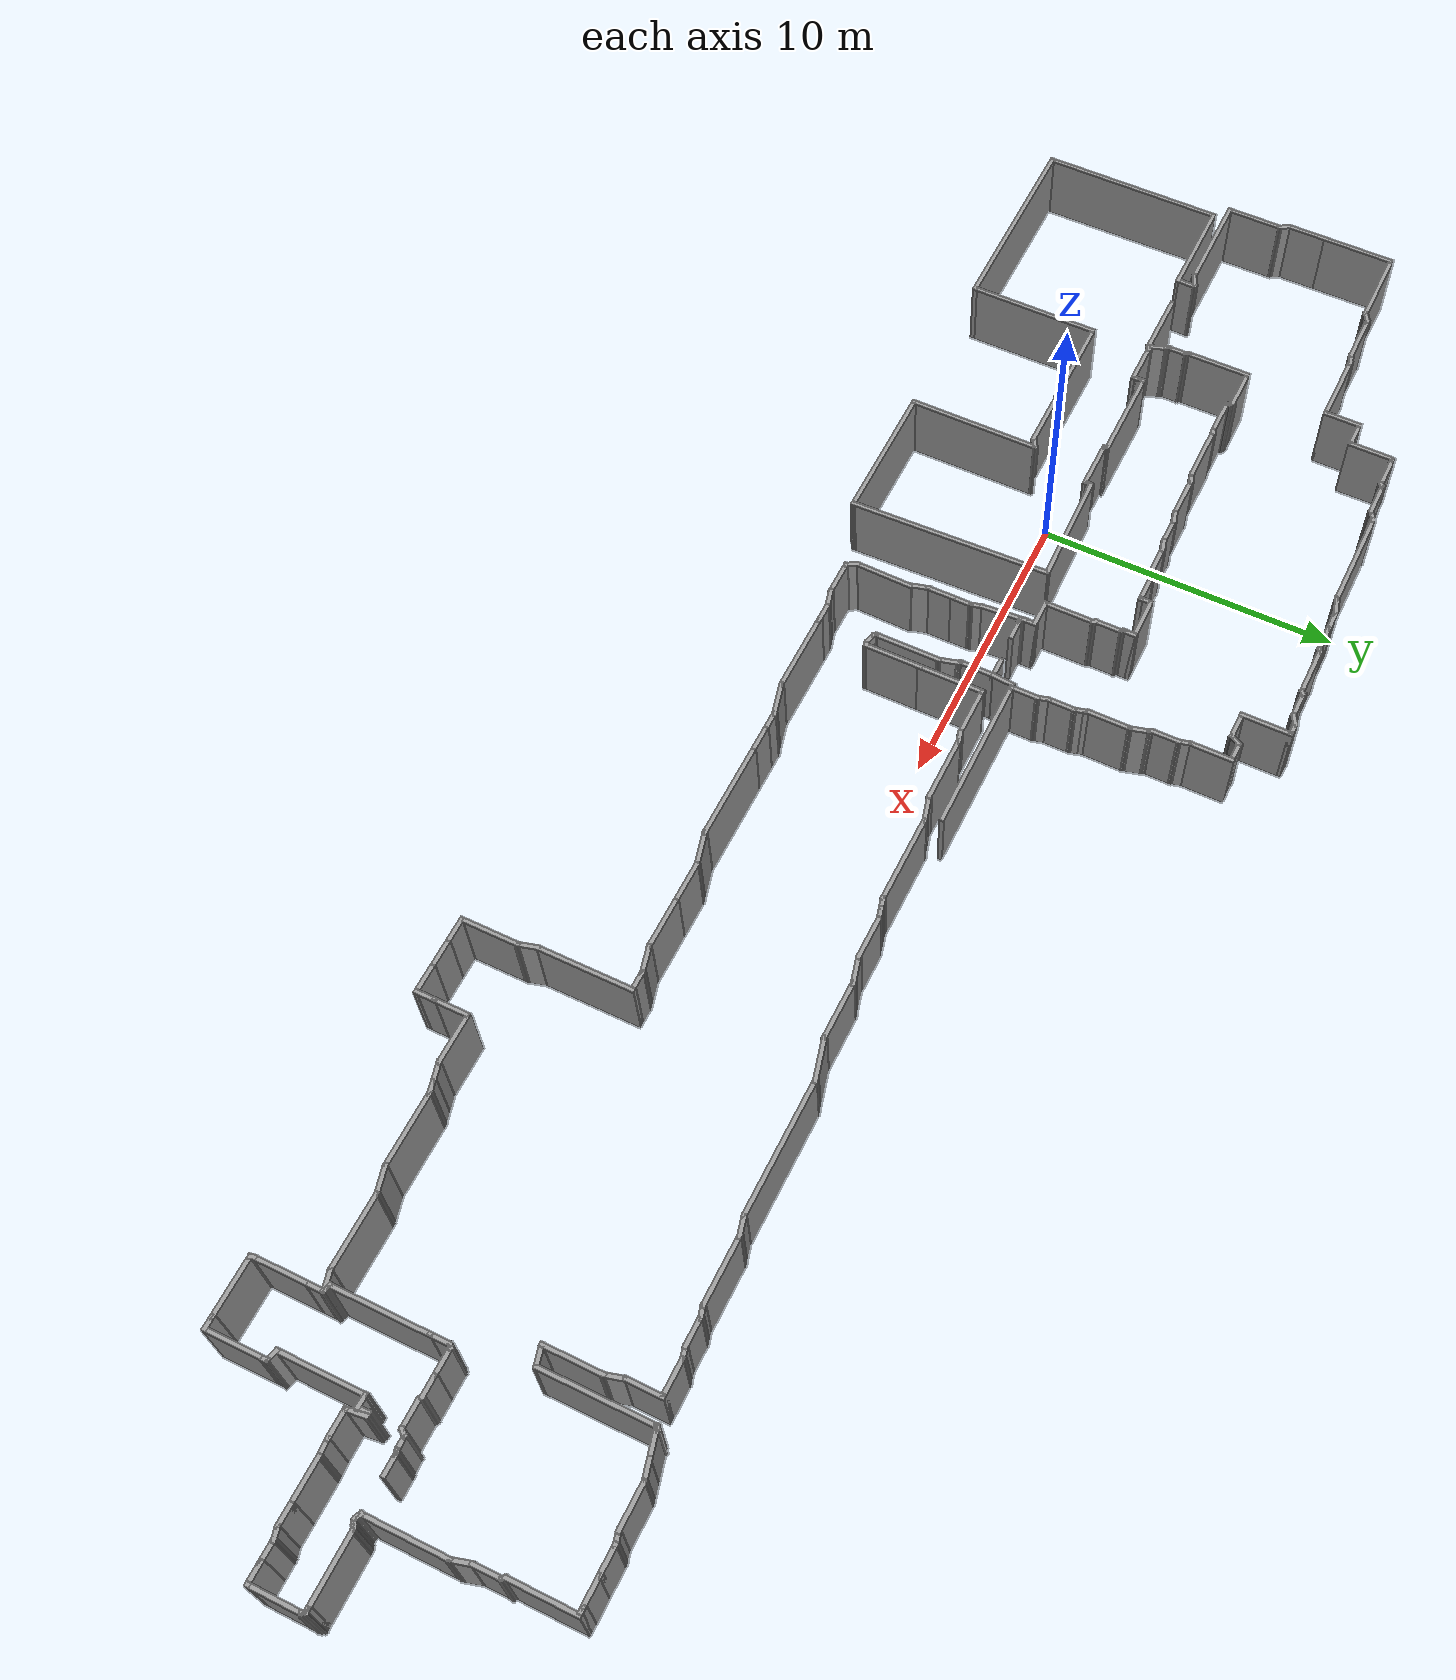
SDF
<?xml version='1.0'?>
<sdf version='1.7'>
  <model name='robovisor_env2'>
    <pose>13.0565 0.516666 0 0 -0 0</pose>
    <link name='Wall_0'>
      <collision name='Wall_0_Collision'>
        <geometry>
          <box>
            <size>0.5 0.15 2.5</size>
          </box>
        </geometry>
        <pose>0 0 1.25 0 -0 0</pose>
      </collision>
      <visual name='Wall_0_Visual'>
        <pose>0 0 1.25 0 -0 0</pose>
        <geometry>
          <box>
            <size>0.5 0.15 2.5</size>
          </box>
        </geometry>
        <material>
          <script>
            <uri>file://media/materials/scripts/gazebo.material</uri>
            <name>Gazebo/Grey</name>
          </script>
          <ambient>1 1 1 1</ambient>
        </material>
        <meta>
          <layer>0</layer>
        </meta>
      </visual>
      <pose>-18.4525 0.304932 0 0 -0 1.5708</pose>
    </link>
    <link name='Wall_1'>
      <collision name='Wall_1_Collision'>
        <geometry>
          <box>
            <size>3.25 0.15 2.5</size>
          </box>
        </geometry>
        <pose>0 0 1.25 0 -0 0</pose>
      </collision>
      <visual name='Wall_1_Visual'>
        <pose>0 0 1.25 0 -0 0</pose>
        <geometry>
          <box>
            <size>3.25 0.15 2.5</size>
          </box>
        </geometry>
        <material>
          <script>
            <uri>file://media/materials/scripts/gazebo.material</uri>
            <name>Gazebo/Grey</name>
          </script>
          <ambient>1 1 1 1</ambient>
        </material>
        <meta>
          <layer>0</layer>
        </meta>
      </visual>
      <pose>-16.9025 0.479932 0 0 -0 0</pose>
    </link>
    <link name='Wall_101'>
      <collision name='Wall_101_Collision'>
        <geometry>
          <box>
            <size>0.25 0.15 2.5</size>
          </box>
        </geometry>
        <pose>0 0 1.25 0 -0 0</pose>
      </collision>
      <visual name='Wall_101_Visual'>
        <pose>0 0 1.25 0 -0 0</pose>
        <geometry>
          <box>
            <size>0.25 0.15 2.5</size>
          </box>
        </geometry>
        <material>
          <script>
            <uri>file://media/materials/scripts/gazebo.material</uri>
            <name>Gazebo/Grey</name>
          </script>
          <ambient>1 1 1 1</ambient>
        </material>
        <meta>
          <layer>0</layer>
        </meta>
      </visual>
      <pose>-5.62434 1.40609 0 0 -0 3.14159</pose>
    </link>
    <link name='Wall_105'>
      <collision name='Wall_105_Collision'>
        <geometry>
          <box>
            <size>0.75 0.15 2.5</size>
          </box>
        </geometry>
        <pose>0 0 1.25 0 -0 0</pose>
      </collision>
      <visual name='Wall_105_Visual'>
        <pose>0 0 1.25 0 -0 0</pose>
        <geometry>
          <box>
            <size>0.75 0.15 2.5</size>
          </box>
        </geometry>
        <material>
          <script>
            <uri>file://media/materials/scripts/gazebo.material</uri>
            <name>Gazebo/Grey</name>
          </script>
          <ambient>1 1 1 1</ambient>
        </material>
        <meta>
          <layer>0</layer>
        </meta>
      </visual>
      <pose>-6.03532 0.716268 0 0 -0 0</pose>
    </link>
    <link name='Wall_110'>
      <collision name='Wall_110_Collision'>
        <geometry>
          <box>
            <size>0.842512 0.15 2.5</size>
          </box>
        </geometry>
        <pose>0 0 1.25 0 -0 0</pose>
      </collision>
      <visual name='Wall_110_Visual'>
        <pose>0 0 1.25 0 -0 0</pose>
        <geometry>
          <box>
            <size>0.842512 0.15 2.5</size>
          </box>
        </geometry>
        <material>
          <script>
            <uri>file://media/materials/scripts/gazebo.material</uri>
            <name>Gazebo/Grey</name>
          </script>
          <ambient>1 1 1 1</ambient>
        </material>
        <meta>
          <layer>0</layer>
        </meta>
      </visual>
      <pose>-5.70483 1.06118 0 0 -0 1.48262</pose>
    </link>
    <link name='Wall_112'>
      <collision name='Wall_112_Collision'>
        <geometry>
          <box>
            <size>0.75 0.15 2.5</size>
          </box>
        </geometry>
        <pose>0 0 1.25 0 -0 0</pose>
      </collision>
      <visual name='Wall_112_Visual'>
        <pose>0 0 1.25 0 -0 0</pose>
        <geometry>
          <box>
            <size>0.75 0.15 2.5</size>
          </box>
        </geometry>
        <material>
          <script>
            <uri>file://media/materials/scripts/gazebo.material</uri>
            <name>Gazebo/Grey</name>
          </script>
          <ambient>1 1 1 1</ambient>
        </material>
        <meta>
          <layer>0</layer>
        </meta>
      </visual>
      <pose>-7.58545 0.639279 0 0 -0 3.14159</pose>
    </link>
    <link name='Wall_113'>
      <collision name='Wall_113_Collision'>
        <geometry>
          <box>
            <size>0.25 0.15 2.5</size>
          </box>
        </geometry>
        <pose>0 0 1.25 0 -0 0</pose>
      </collision>
      <visual name='Wall_113_Visual'>
        <pose>0 0 1.25 0 -0 0</pose>
        <geometry>
          <box>
            <size>0.25 0.15 2.5</size>
          </box>
        </geometry>
        <material>
          <script>
            <uri>file://media/materials/scripts/gazebo.material</uri>
            <name>Gazebo/Grey</name>
          </script>
          <ambient>1 1 1 1</ambient>
        </material>
        <meta>
          <layer>0</layer>
        </meta>
      </visual>
      <pose>-7.93375 0.65222 0 0 -0 2.87979</pose>
    </link>
    <link name='Wall_114'>
      <collision name='Wall_114_Collision'>
        <geometry>
          <box>
            <size>0.25 0.15 2.5</size>
          </box>
        </geometry>
        <pose>0 0 1.25 0 -0 0</pose>
      </collision>
      <visual name='Wall_114_Visual'>
        <pose>0 0 1.25 0 -0 0</pose>
        <geometry>
          <box>
            <size>0.25 0.15 2.5</size>
          </box>
        </geometry>
        <material>
          <script>
            <uri>file://media/materials/scripts/gazebo.material</uri>
            <name>Gazebo/Grey</name>
          </script>
          <ambient>1 1 1 1</ambient>
        </material>
        <meta>
          <layer>0</layer>
        </meta>
      </visual>
      <pose>-8.00704 0.708463 0 0 -0 2.0944</pose>
    </link>
    <link name='Wall_115'>
      <collision name='Wall_115_Collision'>
        <geometry>
          <box>
            <size>0.5 0.15 2.5</size>
          </box>
        </geometry>
        <pose>0 0 1.25 0 -0 0</pose>
      </collision>
      <visual name='Wall_115_Visual'>
        <pose>0 0 1.25 0 -0 0</pose>
        <geometry>
          <box>
            <size>0.5 0.15 2.5</size>
          </box>
        </geometry>
        <material>
          <script>
            <uri>file://media/materials/scripts/gazebo.material</uri>
            <name>Gazebo/Grey</name>
          </script>
          <ambient>1 1 1 1</ambient>
        </material>
        <meta>
          <layer>0</layer>
        </meta>
      </visual>
      <pose>-8.03204 0.926764 0 0 -0 1.5708</pose>
    </link>
    <link name='Wall_116'>
      <collision name='Wall_116_Collision'>
        <geometry>
          <box>
            <size>1 0.15 2.5</size>
          </box>
        </geometry>
        <pose>0 0 1.25 0 -0 0</pose>
      </collision>
      <visual name='Wall_116_Visual'>
        <pose>0 0 1.25 0 -0 0</pose>
        <geometry>
          <box>
            <size>1 0.15 2.5</size>
          </box>
        </geometry>
        <material>
          <script>
            <uri>file://media/materials/scripts/gazebo.material</uri>
            <name>Gazebo/Grey</name>
          </script>
          <ambient>1 1 1 1</ambient>
        </material>
        <meta>
          <layer>0</layer>
        </meta>
      </visual>
      <pose>-8.45704 1.10176 0 0 -0 3.14159</pose>
    </link>
    <link name='Wall_117'>
      <collision name='Wall_117_Collision'>
        <geometry>
          <box>
            <size>1.75 0.15 2.5</size>
          </box>
        </geometry>
        <pose>0 0 1.25 0 -0 0</pose>
      </collision>
      <visual name='Wall_117_Visual'>
        <pose>0 0 1.25 0 -0 0</pose>
        <geometry>
          <box>
            <size>1.75 0.15 2.5</size>
          </box>
        </geometry>
        <material>
          <script>
            <uri>file://media/materials/scripts/gazebo.material</uri>
            <name>Gazebo/Grey</name>
          </script>
          <ambient>1 1 1 1</ambient>
        </material>
        <meta>
          <layer>0</layer>
        </meta>
      </visual>
      <pose>-8.88204 1.90176 0 0 -0 1.5708</pose>
    </link>
    <link name='Wall_119'>
      <collision name='Wall_119_Collision'>
        <geometry>
          <box>
            <size>0.25 0.15 2.5</size>
          </box>
        </geometry>
        <pose>0 0 1.25 0 -0 0</pose>
      </collision>
      <visual name='Wall_119_Visual'>
        <pose>0 0 1.25 0 -0 0</pose>
        <geometry>
          <box>
            <size>0.25 0.15 2.5</size>
          </box>
        </geometry>
        <material>
          <script>
            <uri>file://media/materials/scripts/gazebo.material</uri>
            <name>Gazebo/Grey</name>
          </script>
          <ambient>1 1 1 1</ambient>
        </material>
        <meta>
          <layer>0</layer>
        </meta>
      </visual>
      <pose>-8.90704 2.74506 0 0 -0 2.0944</pose>
    </link>
    <link name='Wall_120'>
      <collision name='Wall_120_Collision'>
        <geometry>
          <box>
            <size>1 0.15 2.5</size>
          </box>
        </geometry>
        <pose>0 0 1.25 0 -0 0</pose>
      </collision>
      <visual name='Wall_120_Visual'>
        <pose>0 0 1.25 0 -0 0</pose>
        <geometry>
          <box>
            <size>1 0.15 2.5</size>
          </box>
        </geometry>
        <material>
          <script>
            <uri>file://media/materials/scripts/gazebo.material</uri>
            <name>Gazebo/Grey</name>
          </script>
          <ambient>1 1 1 1</ambient>
        </material>
        <meta>
          <layer>0</layer>
        </meta>
      </visual>
      <pose>-8.93204 3.21337 0 0 -0 1.5708</pose>
    </link>
    <link name='Wall_121'>
      <collision name='Wall_121_Collision'>
        <geometry>
          <box>
            <size>0.25 0.15 2.5</size>
          </box>
        </geometry>
        <pose>0 0 1.25 0 -0 0</pose>
      </collision>
      <visual name='Wall_121_Visual'>
        <pose>0 0 1.25 0 -0 0</pose>
        <geometry>
          <box>
            <size>0.25 0.15 2.5</size>
          </box>
        </geometry>
        <material>
          <script>
            <uri>file://media/materials/scripts/gazebo.material</uri>
            <name>Gazebo/Grey</name>
          </script>
          <ambient>1 1 1 1</ambient>
        </material>
        <meta>
          <layer>0</layer>
        </meta>
      </visual>
      <pose>-8.95704 3.68167 0 0 -0 2.0944</pose>
    </link>
    <link name='Wall_122'>
      <collision name='Wall_122_Collision'>
        <geometry>
          <box>
            <size>0.5 0.15 2.5</size>
          </box>
        </geometry>
        <pose>0 0 1.25 0 -0 0</pose>
      </collision>
      <visual name='Wall_122_Visual'>
        <pose>0 0 1.25 0 -0 0</pose>
        <geometry>
          <box>
            <size>0.5 0.15 2.5</size>
          </box>
        </geometry>
        <material>
          <script>
            <uri>file://media/materials/scripts/gazebo.material</uri>
            <name>Gazebo/Grey</name>
          </script>
          <ambient>1 1 1 1</ambient>
        </material>
        <meta>
          <layer>0</layer>
        </meta>
      </visual>
      <pose>-8.98204 3.89997 0 0 -0 1.5708</pose>
    </link>
    <link name='Wall_123'>
      <collision name='Wall_123_Collision'>
        <geometry>
          <box>
            <size>1.5 0.15 2.5</size>
          </box>
        </geometry>
        <pose>0 0 1.25 0 -0 0</pose>
      </collision>
      <visual name='Wall_123_Visual'>
        <pose>0 0 1.25 0 -0 0</pose>
        <geometry>
          <box>
            <size>1.5 0.15 2.5</size>
          </box>
        </geometry>
        <material>
          <script>
            <uri>file://media/materials/scripts/gazebo.material</uri>
            <name>Gazebo/Grey</name>
          </script>
          <ambient>1 1 1 1</ambient>
        </material>
        <meta>
          <layer>0</layer>
        </meta>
      </visual>
      <pose>-9.65704 4.07497 0 0 -0 3.14159</pose>
    </link>
    <link name='Wall_124'>
      <collision name='Wall_124_Collision'>
        <geometry>
          <box>
            <size>0.5 0.15 2.5</size>
          </box>
        </geometry>
        <pose>0 0 1.25 0 -0 0</pose>
      </collision>
      <visual name='Wall_124_Visual'>
        <pose>0 0 1.25 0 -0 0</pose>
        <geometry>
          <box>
            <size>0.5 0.15 2.5</size>
          </box>
        </geometry>
        <material>
          <script>
            <uri>file://media/materials/scripts/gazebo.material</uri>
            <name>Gazebo/Grey</name>
          </script>
          <ambient>1 1 1 1</ambient>
        </material>
        <meta>
          <layer>0</layer>
        </meta>
      </visual>
      <pose>-10.332 3.89997 0 0 -0 -1.5708</pose>
    </link>
    <link name='Wall_126'>
      <collision name='Wall_126_Collision'>
        <geometry>
          <box>
            <size>1 0.15 2.5</size>
          </box>
        </geometry>
        <pose>0 0 1.25 0 -0 0</pose>
      </collision>
      <visual name='Wall_126_Visual'>
        <pose>0 0 1.25 0 -0 0</pose>
        <geometry>
          <box>
            <size>1 0.15 2.5</size>
          </box>
        </geometry>
        <material>
          <script>
            <uri>file://media/materials/scripts/gazebo.material</uri>
            <name>Gazebo/Grey</name>
          </script>
          <ambient>1 1 1 1</ambient>
        </material>
        <meta>
          <layer>0</layer>
        </meta>
      </visual>
      <pose>-10.757 3.72497 0 0 -0 3.14159</pose>
    </link>
    <link name='Wall_127'>
      <collision name='Wall_127_Collision'>
        <geometry>
          <box>
            <size>0.5 0.15 2.5</size>
          </box>
        </geometry>
        <pose>0 0 1.25 0 -0 0</pose>
      </collision>
      <visual name='Wall_127_Visual'>
        <pose>0 0 1.25 0 -0 0</pose>
        <geometry>
          <box>
            <size>0.5 0.15 2.5</size>
          </box>
        </geometry>
        <material>
          <script>
            <uri>file://media/materials/scripts/gazebo.material</uri>
            <name>Gazebo/Grey</name>
          </script>
          <ambient>1 1 1 1</ambient>
        </material>
        <meta>
          <layer>0</layer>
        </meta>
      </visual>
      <pose>-11.3511 3.67968 0 0 -0 -2.87979</pose>
    </link>
    <link name='Wall_128'>
      <collision name='Wall_128_Collision'>
        <geometry>
          <box>
            <size>1 0.15 2.5</size>
          </box>
        </geometry>
        <pose>0 0 1.25 0 -0 0</pose>
      </collision>
      <visual name='Wall_128_Visual'>
        <pose>0 0 1.25 0 -0 0</pose>
        <geometry>
          <box>
            <size>1 0.15 2.5</size>
          </box>
        </geometry>
        <material>
          <script>
            <uri>file://media/materials/scripts/gazebo.material</uri>
            <name>Gazebo/Grey</name>
          </script>
          <ambient>1 1 1 1</ambient>
        </material>
        <meta>
          <layer>0</layer>
        </meta>
      </visual>
      <pose>-11.9451 3.63438 0 0 -0 3.14159</pose>
    </link>
    <link name='Wall_129'>
      <collision name='Wall_129_Collision'>
        <geometry>
          <box>
            <size>0.5 0.15 2.5</size>
          </box>
        </geometry>
        <pose>0 0 1.25 0 -0 0</pose>
      </collision>
      <visual name='Wall_129_Visual'>
        <pose>0 0 1.25 0 -0 0</pose>
        <geometry>
          <box>
            <size>0.5 0.15 2.5</size>
          </box>
        </geometry>
        <material>
          <script>
            <uri>file://media/materials/scripts/gazebo.material</uri>
            <name>Gazebo/Grey</name>
          </script>
          <ambient>1 1 1 1</ambient>
        </material>
        <meta>
          <layer>0</layer>
        </meta>
      </visual>
      <pose>-12.5392 3.58909 0 0 -0 -2.87979</pose>
    </link>
    <link name='Wall_13'>
      <collision name='Wall_13_Collision'>
        <geometry>
          <box>
            <size>3.92846 0.15 2.5</size>
          </box>
        </geometry>
        <pose>0 0 1.25 0 -0 0</pose>
      </collision>
      <visual name='Wall_13_Visual'>
        <pose>0 0 1.25 0 -0 0</pose>
        <geometry>
          <box>
            <size>3.92846 0.15 2.5</size>
          </box>
        </geometry>
        <material>
          <script>
            <uri>file://media/materials/scripts/gazebo.material</uri>
            <name>Gazebo/Grey</name>
          </script>
          <ambient>1 1 1 1</ambient>
        </material>
        <meta>
          <layer>0</layer>
        </meta>
      </visual>
      <pose>-11.8641 0.634129 0 0 -0 -3.1129</pose>
    </link>
    <link name='Wall_130'>
      <collision name='Wall_130_Collision'>
        <geometry>
          <box>
            <size>1 0.15 2.5</size>
          </box>
        </geometry>
        <pose>0 0 1.25 0 -0 0</pose>
      </collision>
      <visual name='Wall_130_Visual'>
        <pose>0 0 1.25 0 -0 0</pose>
        <geometry>
          <box>
            <size>1 0.15 2.5</size>
          </box>
        </geometry>
        <material>
          <script>
            <uri>file://media/materials/scripts/gazebo.material</uri>
            <name>Gazebo/Grey</name>
          </script>
          <ambient>1 1 1 1</ambient>
        </material>
        <meta>
          <layer>0</layer>
        </meta>
      </visual>
      <pose>-13.1332 3.5438 0 0 -0 3.14159</pose>
    </link>
    <link name='Wall_131'>
      <collision name='Wall_131_Collision'>
        <geometry>
          <box>
            <size>0.5 0.15 2.5</size>
          </box>
        </geometry>
        <pose>0 0 1.25 0 -0 0</pose>
      </collision>
      <visual name='Wall_131_Visual'>
        <pose>0 0 1.25 0 -0 0</pose>
        <geometry>
          <box>
            <size>0.5 0.15 2.5</size>
          </box>
        </geometry>
        <material>
          <script>
            <uri>file://media/materials/scripts/gazebo.material</uri>
            <name>Gazebo/Grey</name>
          </script>
          <ambient>1 1 1 1</ambient>
        </material>
        <meta>
          <layer>0</layer>
        </meta>
      </visual>
      <pose>-13.7272 3.4985 0 0 -0 -2.87979</pose>
    </link>
    <link name='Wall_132'>
      <collision name='Wall_132_Collision'>
        <geometry>
          <box>
            <size>1.5 0.15 2.5</size>
          </box>
        </geometry>
        <pose>0 0 1.25 0 -0 0</pose>
      </collision>
      <visual name='Wall_132_Visual'>
        <pose>0 0 1.25 0 -0 0</pose>
        <geometry>
          <box>
            <size>1.5 0.15 2.5</size>
          </box>
        </geometry>
        <material>
          <script>
            <uri>file://media/materials/scripts/gazebo.material</uri>
            <name>Gazebo/Grey</name>
          </script>
          <ambient>1 1 1 1</ambient>
        </material>
        <meta>
          <layer>0</layer>
        </meta>
      </visual>
      <pose>-14.5713 3.45321 0 0 -0 3.14159</pose>
    </link>
    <link name='Wall_133'>
      <collision name='Wall_133_Collision'>
        <geometry>
          <box>
            <size>0.5 0.15 2.5</size>
          </box>
        </geometry>
        <pose>0 0 1.25 0 -0 0</pose>
      </collision>
      <visual name='Wall_133_Visual'>
        <pose>0 0 1.25 0 -0 0</pose>
        <geometry>
          <box>
            <size>0.5 0.15 2.5</size>
          </box>
        </geometry>
        <material>
          <script>
            <uri>file://media/materials/scripts/gazebo.material</uri>
            <name>Gazebo/Grey</name>
          </script>
          <ambient>1 1 1 1</ambient>
        </material>
        <meta>
          <layer>0</layer>
        </meta>
      </visual>
      <pose>-15.4153 3.40792 0 0 -0 -2.87979</pose>
    </link>
    <link name='Wall_134'>
      <collision name='Wall_134_Collision'>
        <geometry>
          <box>
            <size>2 0.15 2.5</size>
          </box>
        </geometry>
        <pose>0 0 1.25 0 -0 0</pose>
      </collision>
      <visual name='Wall_134_Visual'>
        <pose>0 0 1.25 0 -0 0</pose>
        <geometry>
          <box>
            <size>2 0.15 2.5</size>
          </box>
        </geometry>
        <material>
          <script>
            <uri>file://media/materials/scripts/gazebo.material</uri>
            <name>Gazebo/Grey</name>
          </script>
          <ambient>1 1 1 1</ambient>
        </material>
        <meta>
          <layer>0</layer>
        </meta>
      </visual>
      <pose>-16.5093 3.36262 0 0 -0 3.14159</pose>
    </link>
    <link name='Wall_135'>
      <collision name='Wall_135_Collision'>
        <geometry>
          <box>
            <size>0.25 0.15 2.5</size>
          </box>
        </geometry>
        <pose>0 0 1.25 0 -0 0</pose>
      </collision>
      <visual name='Wall_135_Visual'>
        <pose>0 0 1.25 0 -0 0</pose>
        <geometry>
          <box>
            <size>0.25 0.15 2.5</size>
          </box>
        </geometry>
        <material>
          <script>
            <uri>file://media/materials/scripts/gazebo.material</uri>
            <name>Gazebo/Grey</name>
          </script>
          <ambient>1 1 1 1</ambient>
        </material>
        <meta>
          <layer>0</layer>
        </meta>
      </visual>
      <pose>-17.4826 3.34968 0 0 -0 -2.87979</pose>
    </link>
    <link name='Wall_136'>
      <collision name='Wall_136_Collision'>
        <geometry>
          <box>
            <size>1.25 0.15 2.5</size>
          </box>
        </geometry>
        <pose>0 0 1.25 0 -0 0</pose>
      </collision>
      <visual name='Wall_136_Visual'>
        <pose>0 0 1.25 0 -0 0</pose>
        <geometry>
          <box>
            <size>1.25 0.15 2.5</size>
          </box>
        </geometry>
        <material>
          <script>
            <uri>file://media/materials/scripts/gazebo.material</uri>
            <name>Gazebo/Grey</name>
          </script>
          <ambient>1 1 1 1</ambient>
        </material>
        <meta>
          <layer>0</layer>
        </meta>
      </visual>
      <pose>-18.0809 3.33674 0 0 -0 3.14159</pose>
    </link>
    <link name='Wall_137'>
      <collision name='Wall_137_Collision'>
        <geometry>
          <box>
            <size>0.25 0.15 2.5</size>
          </box>
        </geometry>
        <pose>0 0 1.25 0 -0 0</pose>
      </collision>
      <visual name='Wall_137_Visual'>
        <pose>0 0 1.25 0 -0 0</pose>
        <geometry>
          <box>
            <size>0.25 0.15 2.5</size>
          </box>
        </geometry>
        <material>
          <script>
            <uri>file://media/materials/scripts/gazebo.material</uri>
            <name>Gazebo/Grey</name>
          </script>
          <ambient>1 1 1 1</ambient>
        </material>
        <meta>
          <layer>0</layer>
        </meta>
      </visual>
      <pose>-18.6792 3.34968 0 0 -0 2.87979</pose>
    </link>
    <link name='Wall_138'>
      <collision name='Wall_138_Collision'>
        <geometry>
          <box>
            <size>0.25 0.15 2.5</size>
          </box>
        </geometry>
        <pose>0 0 1.25 0 -0 0</pose>
      </collision>
      <visual name='Wall_138_Visual'>
        <pose>0 0 1.25 0 -0 0</pose>
        <geometry>
          <box>
            <size>0.25 0.15 2.5</size>
          </box>
        </geometry>
        <material>
          <script>
            <uri>file://media/materials/scripts/gazebo.material</uri>
            <name>Gazebo/Grey</name>
          </script>
          <ambient>1 1 1 1</ambient>
        </material>
        <meta>
          <layer>0</layer>
        </meta>
      </visual>
      <pose>-18.7405 3.41092 0 0 -0 1.8326</pose>
    </link>
    <link name='Wall_139'>
      <collision name='Wall_139_Collision'>
        <geometry>
          <box>
            <size>0.25 0.15 2.5</size>
          </box>
        </geometry>
        <pose>0 0 1.25 0 -0 0</pose>
      </collision>
      <visual name='Wall_139_Visual'>
        <pose>0 0 1.25 0 -0 0</pose>
        <geometry>
          <box>
            <size>0.25 0.15 2.5</size>
          </box>
        </geometry>
        <material>
          <script>
            <uri>file://media/materials/scripts/gazebo.material</uri>
            <name>Gazebo/Grey</name>
          </script>
          <ambient>1 1 1 1</ambient>
        </material>
        <meta>
          <layer>0</layer>
        </meta>
      </visual>
      <pose>-18.7967 3.48421 0 0 -0 2.61799</pose>
    </link>
    <link name='Wall_140'>
      <collision name='Wall_140_Collision'>
        <geometry>
          <box>
            <size>1.5 0.15 2.5</size>
          </box>
        </geometry>
        <pose>0 0 1.25 0 -0 0</pose>
      </collision>
      <visual name='Wall_140_Visual'>
        <pose>0 0 1.25 0 -0 0</pose>
        <geometry>
          <box>
            <size>1.5 0.15 2.5</size>
          </box>
        </geometry>
        <material>
          <script>
            <uri>file://media/materials/scripts/gazebo.material</uri>
            <name>Gazebo/Grey</name>
          </script>
          <ambient>1 1 1 1</ambient>
        </material>
        <meta>
          <layer>0</layer>
        </meta>
      </visual>
      <pose>-19.515 3.50922 0 0 -0 3.14159</pose>
    </link>
    <link name='Wall_141'>
      <collision name='Wall_141_Collision'>
        <geometry>
          <box>
            <size>2.25 0.15 2.5</size>
          </box>
        </geometry>
        <pose>0 0 1.25 0 -0 0</pose>
      </collision>
      <visual name='Wall_141_Visual'>
        <pose>0 0 1.25 0 -0 0</pose>
        <geometry>
          <box>
            <size>2.25 0.15 2.5</size>
          </box>
        </geometry>
        <material>
          <script>
            <uri>file://media/materials/scripts/gazebo.material</uri>
            <name>Gazebo/Grey</name>
          </script>
          <ambient>1 1 1 1</ambient>
        </material>
        <meta>
          <layer>0</layer>
        </meta>
      </visual>
      <pose>-20.19 2.45921 0 0 -0 -1.5708</pose>
    </link>
    <link name='Wall_144'>
      <collision name='Wall_144_Collision'>
        <geometry>
          <box>
            <size>0.25 0.15 2.5</size>
          </box>
        </geometry>
        <pose>0 0 1.25 0 -0 0</pose>
      </collision>
      <visual name='Wall_144_Visual'>
        <pose>0 0 1.25 0 -0 0</pose>
        <geometry>
          <box>
            <size>0.25 0.15 2.5</size>
          </box>
        </geometry>
        <material>
          <script>
            <uri>file://media/materials/scripts/gazebo.material</uri>
            <name>Gazebo/Grey</name>
          </script>
          <ambient>1 1 1 1</ambient>
        </material>
        <meta>
          <layer>0</layer>
        </meta>
      </visual>
      <pose>-20.165 1.36591 0 0 -0 -1.0472</pose>
    </link>
    <link name='Wall_145'>
      <collision name='Wall_145_Collision'>
        <geometry>
          <box>
            <size>0.75 0.15 2.5</size>
          </box>
        </geometry>
        <pose>0 0 1.25 0 -0 0</pose>
      </collision>
      <visual name='Wall_145_Visual'>
        <pose>0 0 1.25 0 -0 0</pose>
        <geometry>
          <box>
            <size>0.75 0.15 2.5</size>
          </box>
        </geometry>
        <material>
          <script>
            <uri>file://media/materials/scripts/gazebo.material</uri>
            <name>Gazebo/Grey</name>
          </script>
          <ambient>1 1 1 1</ambient>
        </material>
        <meta>
          <layer>0</layer>
        </meta>
      </visual>
      <pose>-20.14 1.02261 0 0 -0 -1.5708</pose>
    </link>
    <link name='Wall_146'>
      <collision name='Wall_146_Collision'>
        <geometry>
          <box>
            <size>0.25 0.15 2.5</size>
          </box>
        </geometry>
        <pose>0 0 1.25 0 -0 0</pose>
      </collision>
      <visual name='Wall_146_Visual'>
        <pose>0 0 1.25 0 -0 0</pose>
        <geometry>
          <box>
            <size>0.25 0.15 2.5</size>
          </box>
        </geometry>
        <material>
          <script>
            <uri>file://media/materials/scripts/gazebo.material</uri>
            <name>Gazebo/Grey</name>
          </script>
          <ambient>1 1 1 1</ambient>
        </material>
        <meta>
          <layer>0</layer>
        </meta>
      </visual>
      <pose>-20.115 0.679311 0 0 -0 -1.0472</pose>
    </link>
    <link name='Wall_147'>
      <collision name='Wall_147_Collision'>
        <geometry>
          <box>
            <size>0.741245 0.15 2.5</size>
          </box>
        </geometry>
        <pose>0 0 1.25 0 -0 0</pose>
      </collision>
      <visual name='Wall_147_Visual'>
        <pose>0 0 1.25 0 -0 0</pose>
        <geometry>
          <box>
            <size>0.741245 0.15 2.5</size>
          </box>
        </geometry>
        <material>
          <script>
            <uri>file://media/materials/scripts/gazebo.material</uri>
            <name>Gazebo/Grey</name>
          </script>
          <ambient>1 1 1 1</ambient>
        </material>
        <meta>
          <layer>0</layer>
        </meta>
      </visual>
      <pose>-19.9896 0.357971 0 0 -0 -1.22416</pose>
    </link>
    <link name='Wall_151'>
      <collision name='Wall_151_Collision'>
        <geometry>
          <box>
            <size>1.25 0.15 2.5</size>
          </box>
        </geometry>
        <pose>0 0 1.25 0 -0 0</pose>
      </collision>
      <visual name='Wall_151_Visual'>
        <pose>0 0 1.25 0 -0 0</pose>
        <geometry>
          <box>
            <size>1.25 0.15 2.5</size>
          </box>
        </geometry>
        <material>
          <script>
            <uri>file://media/materials/scripts/gazebo.material</uri>
            <name>Gazebo/Grey</name>
          </script>
          <ambient>1 1 1 1</ambient>
        </material>
        <meta>
          <layer>0</layer>
        </meta>
      </visual>
      <pose>-5.73532 0.166268 0 0 -0 -1.5708</pose>
    </link>
    <link name='Wall_152'>
      <collision name='Wall_152_Collision'>
        <geometry>
          <box>
            <size>0.25 0.15 2.5</size>
          </box>
        </geometry>
        <pose>0 0 1.25 0 -0 0</pose>
      </collision>
      <visual name='Wall_152_Visual'>
        <pose>0 0 1.25 0 -0 0</pose>
        <geometry>
          <box>
            <size>0.25 0.15 2.5</size>
          </box>
        </geometry>
        <material>
          <script>
            <uri>file://media/materials/scripts/gazebo.material</uri>
            <name>Gazebo/Grey</name>
          </script>
          <ambient>1 1 1 1</ambient>
        </material>
        <meta>
          <layer>0</layer>
        </meta>
      </visual>
      <pose>-5.71032 -0.427033 0 0 -0 -1.0472</pose>
    </link>
    <link name='Wall_153'>
      <collision name='Wall_153_Collision'>
        <geometry>
          <box>
            <size>0.75 0.15 2.5</size>
          </box>
        </geometry>
        <pose>0 0 1.25 0 -0 0</pose>
      </collision>
      <visual name='Wall_153_Visual'>
        <pose>0 0 1.25 0 -0 0</pose>
        <geometry>
          <box>
            <size>0.75 0.15 2.5</size>
          </box>
        </geometry>
        <material>
          <script>
            <uri>file://media/materials/scripts/gazebo.material</uri>
            <name>Gazebo/Grey</name>
          </script>
          <ambient>1 1 1 1</ambient>
        </material>
        <meta>
          <layer>0</layer>
        </meta>
      </visual>
      <pose>-5.60768 -0.760112 0 0 -0 -1.309</pose>
    </link>
    <link name='Wall_154'>
      <collision name='Wall_154_Collision'>
        <geometry>
          <box>
            <size>2.25 0.15 2.5</size>
          </box>
        </geometry>
        <pose>0 0 1.25 0 -0 0</pose>
      </collision>
      <visual name='Wall_154_Visual'>
        <pose>0 0 1.25 0 -0 0</pose>
        <geometry>
          <box>
            <size>2.25 0.15 2.5</size>
          </box>
        </geometry>
        <material>
          <script>
            <uri>file://media/materials/scripts/gazebo.material</uri>
            <name>Gazebo/Grey</name>
          </script>
          <ambient>1 1 1 1</ambient>
        </material>
        <meta>
          <layer>0</layer>
        </meta>
      </visual>
      <pose>-5.53003 -2.09989 0 0 -0 -1.5708</pose>
    </link>
    <link name='Wall_155'>
      <collision name='Wall_155_Collision'>
        <geometry>
          <box>
            <size>0.25 0.15 2.5</size>
          </box>
        </geometry>
        <pose>0 0 1.25 0 -0 0</pose>
      </collision>
      <visual name='Wall_155_Visual'>
        <pose>0 0 1.25 0 -0 0</pose>
        <geometry>
          <box>
            <size>0.25 0.15 2.5</size>
          </box>
        </geometry>
        <material>
          <script>
            <uri>file://media/materials/scripts/gazebo.material</uri>
            <name>Gazebo/Grey</name>
          </script>
          <ambient>1 1 1 1</ambient>
        </material>
        <meta>
          <layer>0</layer>
        </meta>
      </visual>
      <pose>-5.50503 -3.19319 0 0 -0 -1.0472</pose>
    </link>
    <link name='Wall_156'>
      <collision name='Wall_156_Collision'>
        <geometry>
          <box>
            <size>0.5 0.15 2.5</size>
          </box>
        </geometry>
        <pose>0 0 1.25 0 -0 0</pose>
      </collision>
      <visual name='Wall_156_Visual'>
        <pose>0 0 1.25 0 -0 0</pose>
        <geometry>
          <box>
            <size>0.5 0.15 2.5</size>
          </box>
        </geometry>
        <material>
          <script>
            <uri>file://media/materials/scripts/gazebo.material</uri>
            <name>Gazebo/Grey</name>
          </script>
          <ambient>1 1 1 1</ambient>
        </material>
        <meta>
          <layer>0</layer>
        </meta>
      </visual>
      <pose>-5.311 -3.28179 0 0 -0 -0.261799</pose>
    </link>
    <link name='Wall_157'>
      <collision name='Wall_157_Collision'>
        <geometry>
          <box>
            <size>0.25 0.15 2.5</size>
          </box>
        </geometry>
        <pose>0 0 1.25 0 -0 0</pose>
      </collision>
      <visual name='Wall_157_Visual'>
        <pose>0 0 1.25 0 -0 0</pose>
        <geometry>
          <box>
            <size>0.25 0.15 2.5</size>
          </box>
        </geometry>
        <material>
          <script>
            <uri>file://media/materials/scripts/gazebo.material</uri>
            <name>Gazebo/Grey</name>
          </script>
          <ambient>1 1 1 1</ambient>
        </material>
        <meta>
          <layer>0</layer>
        </meta>
      </visual>
      <pose>-5.09366 -3.31414 0 0 -0 0.261799</pose>
    </link>
    <link name='Wall_158'>
      <collision name='Wall_158_Collision'>
        <geometry>
          <box>
            <size>0.15 0.15 2.5</size>
          </box>
        </geometry>
        <pose>0 0 1.25 0 -0 0</pose>
      </collision>
      <visual name='Wall_158_Visual'>
        <pose>0 0 1.25 0 -0 0</pose>
        <geometry>
          <box>
            <size>0.15 0.15 2.5</size>
          </box>
        </geometry>
        <material>
          <script>
            <uri>file://media/materials/scripts/gazebo.material</uri>
            <name>Gazebo/Grey</name>
          </script>
          <ambient>1 1 1 1</ambient>
        </material>
        <meta>
          <layer>0</layer>
        </meta>
      </visual>
      <pose>-5.04537 -3.3012 0 0 -0 0</pose>
    </link>
    <link name='Wall_159'>
      <collision name='Wall_159_Collision'>
        <geometry>
          <box>
            <size>0.15 0.15 2.5</size>
          </box>
        </geometry>
        <pose>0 0 1.25 0 -0 0</pose>
      </collision>
      <visual name='Wall_159_Visual'>
        <pose>0 0 1.25 0 -0 0</pose>
        <geometry>
          <box>
            <size>0.15 0.15 2.5</size>
          </box>
        </geometry>
        <material>
          <script>
            <uri>file://media/materials/scripts/gazebo.material</uri>
            <name>Gazebo/Grey</name>
          </script>
          <ambient>1 1 1 1</ambient>
        </material>
        <meta>
          <layer>0</layer>
        </meta>
      </visual>
      <pose>-5.04537 -3.3012 0 0 -0 0</pose>
    </link>
    <link name='Wall_16'>
      <collision name='Wall_16_Collision'>
        <geometry>
          <box>
            <size>4.5 0.15 2.5</size>
          </box>
        </geometry>
        <pose>0 0 1.25 0 -0 0</pose>
      </collision>
      <visual name='Wall_16_Visual'>
        <pose>0 0 1.25 0 -0 0</pose>
        <geometry>
          <box>
            <size>4.5 0.15 2.5</size>
          </box>
        </geometry>
        <material>
          <script>
            <uri>file://media/materials/scripts/gazebo.material</uri>
            <name>Gazebo/Grey</name>
          </script>
          <ambient>1 1 1 1</ambient>
        </material>
        <meta>
          <layer>0</layer>
        </meta>
      </visual>
      <pose>-14.3741 -3.83787 0 0 -0 -1.5708</pose>
    </link>
    <link name='Wall_160'>
      <collision name='Wall_160_Collision'>
        <geometry>
          <box>
            <size>2 0.15 2.5</size>
          </box>
        </geometry>
        <pose>0 0 1.25 0 -0 0</pose>
      </collision>
      <visual name='Wall_160_Visual'>
        <pose>0 0 1.25 0 -0 0</pose>
        <geometry>
          <box>
            <size>2 0.15 2.5</size>
          </box>
        </geometry>
        <material>
          <script>
            <uri>file://media/materials/scripts/gazebo.material</uri>
            <name>Gazebo/Grey</name>
          </script>
          <ambient>1 1 1 1</ambient>
        </material>
        <meta>
          <layer>0</layer>
        </meta>
      </visual>
      <pose>-5.04537 -2.3762 0 0 -0 1.5708</pose>
    </link>
    <link name='Wall_161'>
      <collision name='Wall_161_Collision'>
        <geometry>
          <box>
            <size>2.25 0.15 2.5</size>
          </box>
        </geometry>
        <pose>0 0 1.25 0 -0 0</pose>
      </collision>
      <visual name='Wall_161_Visual'>
        <pose>0 0 1.25 0 -0 0</pose>
        <geometry>
          <box>
            <size>2.25 0.15 2.5</size>
          </box>
        </geometry>
        <material>
          <script>
            <uri>file://media/materials/scripts/gazebo.material</uri>
            <name>Gazebo/Grey</name>
          </script>
          <ambient>1 1 1 1</ambient>
        </material>
        <meta>
          <layer>0</layer>
        </meta>
      </visual>
      <pose>-5.04537 -0.401197 0 0 -0 1.5708</pose>
    </link>
    <link name='Wall_162'>
      <collision name='Wall_162_Collision'>
        <geometry>
          <box>
            <size>1.75 0.15 2.5</size>
          </box>
        </geometry>
        <pose>0 0 1.25 0 -0 0</pose>
      </collision>
      <visual name='Wall_162_Visual'>
        <pose>0 0 1.25 0 -0 0</pose>
        <geometry>
          <box>
            <size>1.75 0.15 2.5</size>
          </box>
        </geometry>
        <material>
          <script>
            <uri>file://media/materials/scripts/gazebo.material</uri>
            <name>Gazebo/Grey</name>
          </script>
          <ambient>1 1 1 1</ambient>
        </material>
        <meta>
          <layer>0</layer>
        </meta>
      </visual>
      <pose>-4.24536 0.648803 0 0 -0 0</pose>
    </link>
    <link name='Wall_163'>
      <collision name='Wall_163_Collision'>
        <geometry>
          <box>
            <size>0.5 0.15 2.5</size>
          </box>
        </geometry>
        <pose>0 0 1.25 0 -0 0</pose>
      </collision>
      <visual name='Wall_163_Visual'>
        <pose>0 0 1.25 0 -0 0</pose>
        <geometry>
          <box>
            <size>0.5 0.15 2.5</size>
          </box>
        </geometry>
        <material>
          <script>
            <uri>file://media/materials/scripts/gazebo.material</uri>
            <name>Gazebo/Grey</name>
          </script>
          <ambient>1 1 1 1</ambient>
        </material>
        <meta>
          <layer>0</layer>
        </meta>
      </visual>
      <pose>-3.27633 0.694096 0 0 -0 0.261799</pose>
    </link>
    <link name='Wall_164'>
      <collision name='Wall_164_Collision'>
        <geometry>
          <box>
            <size>2.25 0.15 2.5</size>
          </box>
        </geometry>
        <pose>0 0 1.25 0 -0 0</pose>
      </collision>
      <visual name='Wall_164_Visual'>
        <pose>0 0 1.25 0 -0 0</pose>
        <geometry>
          <box>
            <size>2.25 0.15 2.5</size>
          </box>
        </geometry>
        <material>
          <script>
            <uri>file://media/materials/scripts/gazebo.material</uri>
            <name>Gazebo/Grey</name>
          </script>
          <ambient>1 1 1 1</ambient>
        </material>
        <meta>
          <layer>0</layer>
        </meta>
      </visual>
      <pose>-2.05729 0.73939 0 0 -0 0</pose>
    </link>
    <link name='Wall_165'>
      <collision name='Wall_165_Collision'>
        <geometry>
          <box>
            <size>1 0.15 2.5</size>
          </box>
        </geometry>
        <pose>0 0 1.25 0 -0 0</pose>
      </collision>
      <visual name='Wall_165_Visual'>
        <pose>0 0 1.25 0 -0 0</pose>
        <geometry>
          <box>
            <size>1 0.15 2.5</size>
          </box>
        </geometry>
        <material>
          <script>
            <uri>file://media/materials/scripts/gazebo.material</uri>
            <name>Gazebo/Grey</name>
          </script>
          <ambient>1 1 1 1</ambient>
        </material>
        <meta>
          <layer>0</layer>
        </meta>
      </visual>
      <pose>-0.596773 0.849388 0 0 -0 0.261799</pose>
    </link>
    <link name='Wall_166'>
      <collision name='Wall_166_Collision'>
        <geometry>
          <box>
            <size>3 0.15 2.5</size>
          </box>
        </geometry>
        <pose>0 0 1.25 0 -0 0</pose>
      </collision>
      <visual name='Wall_166_Visual'>
        <pose>0 0 1.25 0 -0 0</pose>
        <geometry>
          <box>
            <size>3 0.15 2.5</size>
          </box>
        </geometry>
        <material>
          <script>
            <uri>file://media/materials/scripts/gazebo.material</uri>
            <name>Gazebo/Grey</name>
          </script>
          <ambient>1 1 1 1</ambient>
        </material>
        <meta>
          <layer>0</layer>
        </meta>
      </visual>
      <pose>1.23875 0.959386 0 0 -0 0</pose>
    </link>
    <link name='Wall_167'>
      <collision name='Wall_167_Collision'>
        <geometry>
          <box>
            <size>0.5 0.15 2.5</size>
          </box>
        </geometry>
        <pose>0 0 1.25 0 -0 0</pose>
      </collision>
      <visual name='Wall_167_Visual'>
        <pose>0 0 1.25 0 -0 0</pose>
        <geometry>
          <box>
            <size>0.5 0.15 2.5</size>
          </box>
        </geometry>
        <material>
          <script>
            <uri>file://media/materials/scripts/gazebo.material</uri>
            <name>Gazebo/Grey</name>
          </script>
          <ambient>1 1 1 1</ambient>
        </material>
        <meta>
          <layer>0</layer>
        </meta>
      </visual>
      <pose>2.83278 1.00468 0 0 -0 0.261799</pose>
    </link>
    <link name='Wall_168'>
      <collision name='Wall_168_Collision'>
        <geometry>
          <box>
            <size>0.5 0.15 2.5</size>
          </box>
        </geometry>
        <pose>0 0 1.25 0 -0 0</pose>
      </collision>
      <visual name='Wall_168_Visual'>
        <pose>0 0 1.25 0 -0 0</pose>
        <geometry>
          <box>
            <size>0.5 0.15 2.5</size>
          </box>
        </geometry>
        <material>
          <script>
            <uri>file://media/materials/scripts/gazebo.material</uri>
            <name>Gazebo/Grey</name>
          </script>
          <ambient>1 1 1 1</ambient>
        </material>
        <meta>
          <layer>0</layer>
        </meta>
      </visual>
      <pose>3.17086 1.09527 0 0 -0 0.261799</pose>
    </link>
    <link name='Wall_169'>
      <collision name='Wall_169_Collision'>
        <geometry>
          <box>
            <size>1.5 0.15 2.5</size>
          </box>
        </geometry>
        <pose>0 0 1.25 0 -0 0</pose>
      </collision>
      <visual name='Wall_169_Visual'>
        <pose>0 0 1.25 0 -0 0</pose>
        <geometry>
          <box>
            <size>1.5 0.15 2.5</size>
          </box>
        </geometry>
        <material>
          <script>
            <uri>file://media/materials/scripts/gazebo.material</uri>
            <name>Gazebo/Grey</name>
          </script>
          <ambient>1 1 1 1</ambient>
        </material>
        <meta>
          <layer>0</layer>
        </meta>
      </visual>
      <pose>4.01489 1.14056 0 0 -0 0</pose>
    </link>
    <link name='Wall_17'>
      <collision name='Wall_17_Collision'>
        <geometry>
          <box>
            <size>4.75 0.15 2.5</size>
          </box>
        </geometry>
        <pose>0 0 1.25 0 -0 0</pose>
      </collision>
      <visual name='Wall_17_Visual'>
        <pose>0 0 1.25 0 -0 0</pose>
        <geometry>
          <box>
            <size>4.75 0.15 2.5</size>
          </box>
        </geometry>
        <material>
          <script>
            <uri>file://media/materials/scripts/gazebo.material</uri>
            <name>Gazebo/Grey</name>
          </script>
          <ambient>1 1 1 1</ambient>
        </material>
        <meta>
          <layer>0</layer>
        </meta>
      </visual>
      <pose>-12.0741 -6.01287 0 0 -0 0</pose>
    </link>
    <link name='Wall_171'>
      <collision name='Wall_171_Collision'>
        <geometry>
          <box>
            <size>1 0.15 2.5</size>
          </box>
        </geometry>
        <pose>0 0 1.25 0 -0 0</pose>
      </collision>
      <visual name='Wall_171_Visual'>
        <pose>0 0 1.25 0 -0 0</pose>
        <geometry>
          <box>
            <size>1 0.15 2.5</size>
          </box>
        </geometry>
        <material>
          <script>
            <uri>file://media/materials/scripts/gazebo.material</uri>
            <name>Gazebo/Grey</name>
          </script>
          <ambient>1 1 1 1</ambient>
        </material>
        <meta>
          <layer>0</layer>
        </meta>
      </visual>
      <pose>5.10041 1.25056 0 0 -0 0.261799</pose>
    </link>
    <link name='Wall_172'>
      <collision name='Wall_172_Collision'>
        <geometry>
          <box>
            <size>2 0.15 2.5</size>
          </box>
        </geometry>
        <pose>0 0 1.25 0 -0 0</pose>
      </collision>
      <visual name='Wall_172_Visual'>
        <pose>0 0 1.25 0 -0 0</pose>
        <geometry>
          <box>
            <size>2 0.15 2.5</size>
          </box>
        </geometry>
        <material>
          <script>
            <uri>file://media/materials/scripts/gazebo.material</uri>
            <name>Gazebo/Grey</name>
          </script>
          <ambient>1 1 1 1</ambient>
        </material>
        <meta>
          <layer>0</layer>
        </meta>
      </visual>
      <pose>6.43593 1.36055 0 0 -0 0</pose>
    </link>
    <link name='Wall_173'>
      <collision name='Wall_173_Collision'>
        <geometry>
          <box>
            <size>1.5 0.15 2.5</size>
          </box>
        </geometry>
        <pose>0 0 1.25 0 -0 0</pose>
      </collision>
      <visual name='Wall_173_Visual'>
        <pose>0 0 1.25 0 -0 0</pose>
        <geometry>
          <box>
            <size>1.5 0.15 2.5</size>
          </box>
        </geometry>
        <material>
          <script>
            <uri>file://media/materials/scripts/gazebo.material</uri>
            <name>Gazebo/Grey</name>
          </script>
          <ambient>1 1 1 1</ambient>
        </material>
        <meta>
          <layer>0</layer>
        </meta>
      </visual>
      <pose>8.01293 1.53526 0 0 -0 0.261799</pose>
    </link>
    <link name='Wall_174'>
      <collision name='Wall_174_Collision'>
        <geometry>
          <box>
            <size>4.5 0.15 2.5</size>
          </box>
        </geometry>
        <pose>0 0 1.25 0 -0 0</pose>
      </collision>
      <visual name='Wall_174_Visual'>
        <pose>0 0 1.25 0 -0 0</pose>
        <geometry>
          <box>
            <size>4.5 0.15 2.5</size>
          </box>
        </geometry>
        <material>
          <script>
            <uri>file://media/materials/scripts/gazebo.material</uri>
            <name>Gazebo/Grey</name>
          </script>
          <ambient>1 1 1 1</ambient>
        </material>
        <meta>
          <layer>0</layer>
        </meta>
      </visual>
      <pose>10.8399 1.70996 0 0 -0 0</pose>
    </link>
    <link name='Wall_175'>
      <collision name='Wall_175_Collision'>
        <geometry>
          <box>
            <size>0.75 0.15 2.5</size>
          </box>
        </geometry>
        <pose>0 0 1.25 0 -0 0</pose>
      </collision>
      <visual name='Wall_175_Visual'>
        <pose>0 0 1.25 0 -0 0</pose>
        <geometry>
          <box>
            <size>0.75 0.15 2.5</size>
          </box>
        </geometry>
        <material>
          <script>
            <uri>file://media/materials/scripts/gazebo.material</uri>
            <name>Gazebo/Grey</name>
          </script>
          <ambient>1 1 1 1</ambient>
        </material>
        <meta>
          <layer>0</layer>
        </meta>
      </visual>
      <pose>13.3047 1.78761 0 0 -0 0.261799</pose>
    </link>
    <link name='Wall_176'>
      <collision name='Wall_176_Collision'>
        <geometry>
          <box>
            <size>2.25 0.15 2.5</size>
          </box>
        </geometry>
        <pose>0 0 1.25 0 -0 0</pose>
      </collision>
      <visual name='Wall_176_Visual'>
        <pose>0 0 1.25 0 -0 0</pose>
        <geometry>
          <box>
            <size>2.25 0.15 2.5</size>
          </box>
        </geometry>
        <material>
          <script>
            <uri>file://media/materials/scripts/gazebo.material</uri>
            <name>Gazebo/Grey</name>
          </script>
          <ambient>1 1 1 1</ambient>
        </material>
        <meta>
          <layer>0</layer>
        </meta>
      </visual>
      <pose>14.6445 1.86525 0 0 -0 0</pose>
    </link>
    <link name='Wall_177'>
      <collision name='Wall_177_Collision'>
        <geometry>
          <box>
            <size>0.5 0.15 2.5</size>
          </box>
        </geometry>
        <pose>0 0 1.25 0 -0 0</pose>
      </collision>
      <visual name='Wall_177_Visual'>
        <pose>0 0 1.25 0 -0 0</pose>
        <geometry>
          <box>
            <size>0.5 0.15 2.5</size>
          </box>
        </geometry>
        <material>
          <script>
            <uri>file://media/materials/scripts/gazebo.material</uri>
            <name>Gazebo/Grey</name>
          </script>
          <ambient>1 1 1 1</ambient>
        </material>
        <meta>
          <layer>0</layer>
        </meta>
      </visual>
      <pose>15.8635 1.91055 0 0 -0 0.261799</pose>
    </link>
    <link name='Wall_178'>
      <collision name='Wall_178_Collision'>
        <geometry>
          <box>
            <size>1 0.15 2.5</size>
          </box>
        </geometry>
        <pose>0 0 1.25 0 -0 0</pose>
      </collision>
      <visual name='Wall_178_Visual'>
        <pose>0 0 1.25 0 -0 0</pose>
        <geometry>
          <box>
            <size>1 0.15 2.5</size>
          </box>
        </geometry>
        <material>
          <script>
            <uri>file://media/materials/scripts/gazebo.material</uri>
            <name>Gazebo/Grey</name>
          </script>
          <ambient>1 1 1 1</ambient>
        </material>
        <meta>
          <layer>0</layer>
        </meta>
      </visual>
      <pose>16.4576 1.95584 0 0 -0 0</pose>
    </link>
    <link name='Wall_179'>
      <collision name='Wall_179_Collision'>
        <geometry>
          <box>
            <size>0.5 0.15 2.5</size>
          </box>
        </geometry>
        <pose>0 0 1.25 0 -0 0</pose>
      </collision>
      <visual name='Wall_179_Visual'>
        <pose>0 0 1.25 0 -0 0</pose>
        <geometry>
          <box>
            <size>0.5 0.15 2.5</size>
          </box>
        </geometry>
        <material>
          <script>
            <uri>file://media/materials/scripts/gazebo.material</uri>
            <name>Gazebo/Grey</name>
          </script>
          <ambient>1 1 1 1</ambient>
        </material>
        <meta>
          <layer>0</layer>
        </meta>
      </visual>
      <pose>17.0516 2.00113 0 0 -0 0.261799</pose>
    </link>
    <link name='Wall_18'>
      <collision name='Wall_18_Collision'>
        <geometry>
          <box>
            <size>6.85422 0.15 2.5</size>
          </box>
        </geometry>
        <pose>0 0 1.25 0 -0 0</pose>
      </collision>
      <visual name='Wall_18_Visual'>
        <pose>0 0 1.25 0 -0 0</pose>
        <geometry>
          <box>
            <size>6.85422 0.15 2.5</size>
          </box>
        </geometry>
        <material>
          <script>
            <uri>file://media/materials/scripts/gazebo.material</uri>
            <name>Gazebo/Grey</name>
          </script>
          <ambient>1 1 1 1</ambient>
        </material>
        <meta>
          <layer>0</layer>
        </meta>
      </visual>
      <pose>-9.87486 -2.66227 0 0 -0 1.60086</pose>
    </link>
    <link name='Wall_180'>
      <collision name='Wall_180_Collision'>
        <geometry>
          <box>
            <size>1.25 0.15 2.5</size>
          </box>
        </geometry>
        <pose>0 0 1.25 0 -0 0</pose>
      </collision>
      <visual name='Wall_180_Visual'>
        <pose>0 0 1.25 0 -0 0</pose>
        <geometry>
          <box>
            <size>1.25 0.15 2.5</size>
          </box>
        </geometry>
        <material>
          <script>
            <uri>file://media/materials/scripts/gazebo.material</uri>
            <name>Gazebo/Grey</name>
          </script>
          <ambient>1 1 1 1</ambient>
        </material>
        <meta>
          <layer>0</layer>
        </meta>
      </visual>
      <pose>17.7706 2.04643 0 0 -0 0</pose>
    </link>
    <link name='Wall_181'>
      <collision name='Wall_181_Collision'>
        <geometry>
          <box>
            <size>1.25 0.15 2.5</size>
          </box>
        </geometry>
        <pose>0 0 1.25 0 -0 0</pose>
      </collision>
      <visual name='Wall_181_Visual'>
        <pose>0 0 1.25 0 -0 0</pose>
        <geometry>
          <box>
            <size>1.25 0.15 2.5</size>
          </box>
        </geometry>
        <material>
          <script>
            <uri>file://media/materials/scripts/gazebo.material</uri>
            <name>Gazebo/Grey</name>
          </script>
          <ambient>1 1 1 1</ambient>
        </material>
        <meta>
          <layer>0</layer>
        </meta>
      </visual>
      <pose>18.3206 1.49643 0 0 -0 -1.5708</pose>
    </link>
    <link name='Wall_182'>
      <collision name='Wall_182_Collision'>
        <geometry>
          <box>
            <size>0.75 0.15 2.5</size>
          </box>
        </geometry>
        <pose>0 0 1.25 0 -0 0</pose>
      </collision>
      <visual name='Wall_182_Visual'>
        <pose>0 0 1.25 0 -0 0</pose>
        <geometry>
          <box>
            <size>0.75 0.15 2.5</size>
          </box>
        </geometry>
        <material>
          <script>
            <uri>file://media/materials/scripts/gazebo.material</uri>
            <name>Gazebo/Grey</name>
          </script>
          <ambient>1 1 1 1</ambient>
        </material>
        <meta>
          <layer>0</layer>
        </meta>
      </visual>
      <pose>18.3983 0.656648 0 0 -0 -1.309</pose>
    </link>
    <link name='Wall_183'>
      <collision name='Wall_183_Collision'>
        <geometry>
          <box>
            <size>2 0.15 2.5</size>
          </box>
        </geometry>
        <pose>0 0 1.25 0 -0 0</pose>
      </collision>
      <visual name='Wall_183_Visual'>
        <pose>0 0 1.25 0 -0 0</pose>
        <geometry>
          <box>
            <size>2 0.15 2.5</size>
          </box>
        </geometry>
        <material>
          <script>
            <uri>file://media/materials/scripts/gazebo.material</uri>
            <name>Gazebo/Grey</name>
          </script>
          <ambient>1 1 1 1</ambient>
        </material>
        <meta>
          <layer>0</layer>
        </meta>
      </visual>
      <pose>18.4759 -0.55813 0 0 -0 -1.5708</pose>
    </link>
    <link name='Wall_184'>
      <collision name='Wall_184_Collision'>
        <geometry>
          <box>
            <size>0.75 0.15 2.5</size>
          </box>
        </geometry>
        <pose>0 0 1.25 0 -0 0</pose>
      </collision>
      <visual name='Wall_184_Visual'>
        <pose>0 0 1.25 0 -0 0</pose>
        <geometry>
          <box>
            <size>0.75 0.15 2.5</size>
          </box>
        </geometry>
        <material>
          <script>
            <uri>file://media/materials/scripts/gazebo.material</uri>
            <name>Gazebo/Grey</name>
          </script>
          <ambient>1 1 1 1</ambient>
        </material>
        <meta>
          <layer>0</layer>
        </meta>
      </visual>
      <pose>18.7657 -1.40548 0 0 -0 0.261799</pose>
    </link>
    <link name='Wall_185'>
      <collision name='Wall_185_Collision'>
        <geometry>
          <box>
            <size>3.75 0.15 2.5</size>
          </box>
        </geometry>
        <pose>0 0 1.25 0 -0 0</pose>
      </collision>
      <visual name='Wall_185_Visual'>
        <pose>0 0 1.25 0 -0 0</pose>
        <geometry>
          <box>
            <size>3.75 0.15 2.5</size>
          </box>
        </geometry>
        <material>
          <script>
            <uri>file://media/materials/scripts/gazebo.material</uri>
            <name>Gazebo/Grey</name>
          </script>
          <ambient>1 1 1 1</ambient>
        </material>
        <meta>
          <layer>0</layer>
        </meta>
      </visual>
      <pose>19.0555 0.472162 0 0 -0 1.5708</pose>
    </link>
    <link name='Wall_186'>
      <collision name='Wall_186_Collision'>
        <geometry>
          <box>
            <size>0.25 0.15 2.5</size>
          </box>
        </geometry>
        <pose>0 0 1.25 0 -0 0</pose>
      </collision>
      <visual name='Wall_186_Visual'>
        <pose>0 0 1.25 0 -0 0</pose>
        <geometry>
          <box>
            <size>0.25 0.15 2.5</size>
          </box>
        </geometry>
        <material>
          <script>
            <uri>file://media/materials/scripts/gazebo.material</uri>
            <name>Gazebo/Grey</name>
          </script>
          <ambient>1 1 1 1</ambient>
        </material>
        <meta>
          <layer>0</layer>
        </meta>
      </visual>
      <pose>19.0908 2.30752 0 0 -0 0.785398</pose>
    </link>
    <link name='Wall_188'>
      <collision name='Wall_188_Collision'>
        <geometry>
          <box>
            <size>1 0.15 2.5</size>
          </box>
        </geometry>
        <pose>0 0 1.25 0 -0 0</pose>
      </collision>
      <visual name='Wall_188_Visual'>
        <pose>0 0 1.25 0 -0 0</pose>
        <geometry>
          <box>
            <size>1 0.15 2.5</size>
          </box>
        </geometry>
        <material>
          <script>
            <uri>file://media/materials/scripts/gazebo.material</uri>
            <name>Gazebo/Grey</name>
          </script>
          <ambient>1 1 1 1</ambient>
        </material>
        <meta>
          <layer>0</layer>
        </meta>
      </visual>
      <pose>19.466 2.38216 0 0 -0 0.261799</pose>
    </link>
    <link name='Wall_189'>
      <collision name='Wall_189_Collision'>
        <geometry>
          <box>
            <size>0.75 0.15 2.5</size>
          </box>
        </geometry>
        <pose>0 0 1.25 0 -0 0</pose>
      </collision>
      <visual name='Wall_189_Visual'>
        <pose>0 0 1.25 0 -0 0</pose>
        <geometry>
          <box>
            <size>0.75 0.15 2.5</size>
          </box>
        </geometry>
        <material>
          <script>
            <uri>file://media/materials/scripts/gazebo.material</uri>
            <name>Gazebo/Grey</name>
          </script>
          <ambient>1 1 1 1</ambient>
        </material>
        <meta>
          <layer>0</layer>
        </meta>
      </visual>
      <pose>20.1663 2.5698 0 0 -0 0.261799</pose>
    </link>
    <link name='Wall_190'>
      <collision name='Wall_190_Collision'>
        <geometry>
          <box>
            <size>1.5 0.15 2.5</size>
          </box>
        </geometry>
        <pose>0 0 1.25 0 -0 0</pose>
      </collision>
      <visual name='Wall_190_Visual'>
        <pose>0 0 1.25 0 -0 0</pose>
        <geometry>
          <box>
            <size>1.5 0.15 2.5</size>
          </box>
        </geometry>
        <material>
          <script>
            <uri>file://media/materials/scripts/gazebo.material</uri>
            <name>Gazebo/Grey</name>
          </script>
          <ambient>1 1 1 1</ambient>
        </material>
        <meta>
          <layer>0</layer>
        </meta>
      </visual>
      <pose>21.1311 2.64745 0 0 -0 0</pose>
    </link>
    <link name='Wall_191'>
      <collision name='Wall_191_Collision'>
        <geometry>
          <box>
            <size>0.5 0.15 2.5</size>
          </box>
        </geometry>
        <pose>0 0 1.25 0 -0 0</pose>
      </collision>
      <visual name='Wall_191_Visual'>
        <pose>0 0 1.25 0 -0 0</pose>
        <geometry>
          <box>
            <size>0.5 0.15 2.5</size>
          </box>
        </geometry>
        <material>
          <script>
            <uri>file://media/materials/scripts/gazebo.material</uri>
            <name>Gazebo/Grey</name>
          </script>
          <ambient>1 1 1 1</ambient>
        </material>
        <meta>
          <layer>0</layer>
        </meta>
      </visual>
      <pose>21.9751 2.69274 0 0 -0 0.261799</pose>
    </link>
    <link name='Wall_192'>
      <collision name='Wall_192_Collision'>
        <geometry>
          <box>
            <size>1 0.15 2.5</size>
          </box>
        </geometry>
        <pose>0 0 1.25 0 -0 0</pose>
      </collision>
      <visual name='Wall_192_Visual'>
        <pose>0 0 1.25 0 -0 0</pose>
        <geometry>
          <box>
            <size>1 0.15 2.5</size>
          </box>
        </geometry>
        <material>
          <script>
            <uri>file://media/materials/scripts/gazebo.material</uri>
            <name>Gazebo/Grey</name>
          </script>
          <ambient>1 1 1 1</ambient>
        </material>
        <meta>
          <layer>0</layer>
        </meta>
      </visual>
      <pose>22.5691 2.73804 0 0 -0 0</pose>
    </link>
    <link name='Wall_193'>
      <collision name='Wall_193_Collision'>
        <geometry>
          <box>
            <size>1 0.15 2.5</size>
          </box>
        </geometry>
        <pose>0 0 1.25 0 -0 0</pose>
      </collision>
      <visual name='Wall_193_Visual'>
        <pose>0 0 1.25 0 -0 0</pose>
        <geometry>
          <box>
            <size>1 0.15 2.5</size>
          </box>
        </geometry>
        <material>
          <script>
            <uri>file://media/materials/scripts/gazebo.material</uri>
            <name>Gazebo/Grey</name>
          </script>
          <ambient>1 1 1 1</ambient>
        </material>
        <meta>
          <layer>0</layer>
        </meta>
      </visual>
      <pose>23.4191 2.73804 0 0 -0 0</pose>
    </link>
    <link name='Wall_194'>
      <collision name='Wall_194_Collision'>
        <geometry>
          <box>
            <size>0.25 0.15 2.5</size>
          </box>
        </geometry>
        <pose>0 0 1.25 0 -0 0</pose>
      </collision>
      <visual name='Wall_194_Visual'>
        <pose>0 0 1.25 0 -0 0</pose>
        <geometry>
          <box>
            <size>0.25 0.15 2.5</size>
          </box>
        </geometry>
        <material>
          <script>
            <uri>file://media/materials/scripts/gazebo.material</uri>
            <name>Gazebo/Grey</name>
          </script>
          <ambient>1 1 1 1</ambient>
        </material>
        <meta>
          <layer>0</layer>
        </meta>
      </visual>
      <pose>23.8941 2.73804 0 0 -0 0</pose>
    </link>
    <link name='Wall_195'>
      <collision name='Wall_195_Collision'>
        <geometry>
          <box>
            <size>0.25 0.15 2.5</size>
          </box>
        </geometry>
        <pose>0 0 1.25 0 -0 0</pose>
      </collision>
      <visual name='Wall_195_Visual'>
        <pose>0 0 1.25 0 -0 0</pose>
        <geometry>
          <box>
            <size>0.25 0.15 2.5</size>
          </box>
        </geometry>
        <material>
          <script>
            <uri>file://media/materials/scripts/gazebo.material</uri>
            <name>Gazebo/Grey</name>
          </script>
          <ambient>1 1 1 1</ambient>
        </material>
        <meta>
          <layer>0</layer>
        </meta>
      </visual>
      <pose>23.9941 2.73804 0 0 -0 0</pose>
    </link>
    <link name='Wall_196'>
      <collision name='Wall_196_Collision'>
        <geometry>
          <box>
            <size>2.25 0.15 2.5</size>
          </box>
        </geometry>
        <pose>0 0 1.25 0 -0 0</pose>
      </collision>
      <visual name='Wall_196_Visual'>
        <pose>0 0 1.25 0 -0 0</pose>
        <geometry>
          <box>
            <size>2.25 0.15 2.5</size>
          </box>
        </geometry>
        <material>
          <script>
            <uri>file://media/materials/scripts/gazebo.material</uri>
            <name>Gazebo/Grey</name>
          </script>
          <ambient>1 1 1 1</ambient>
        </material>
        <meta>
          <layer>0</layer>
        </meta>
      </visual>
      <pose>24.0441 1.68804 0 0 -0 -1.5708</pose>
    </link>
    <link name='Wall_197'>
      <collision name='Wall_197_Collision'>
        <geometry>
          <box>
            <size>0.25 0.15 2.5</size>
          </box>
        </geometry>
        <pose>0 0 1.25 0 -0 0</pose>
      </collision>
      <visual name='Wall_197_Visual'>
        <pose>0 0 1.25 0 -0 0</pose>
        <geometry>
          <box>
            <size>0.25 0.15 2.5</size>
          </box>
        </geometry>
        <material>
          <script>
            <uri>file://media/materials/scripts/gazebo.material</uri>
            <name>Gazebo/Grey</name>
          </script>
          <ambient>1 1 1 1</ambient>
        </material>
        <meta>
          <layer>0</layer>
        </meta>
      </visual>
      <pose>24.0795 0.602681 0 0 -0 -0.785398</pose>
    </link>
    <link name='Wall_198'>
      <collision name='Wall_198_Collision'>
        <geometry>
          <box>
            <size>1 0.15 2.5</size>
          </box>
        </geometry>
        <pose>0 0 1.25 0 -0 0</pose>
      </collision>
      <visual name='Wall_198_Visual'>
        <pose>0 0 1.25 0 -0 0</pose>
        <geometry>
          <box>
            <size>1 0.15 2.5</size>
          </box>
        </geometry>
        <material>
          <script>
            <uri>file://media/materials/scripts/gazebo.material</uri>
            <name>Gazebo/Grey</name>
          </script>
          <ambient>1 1 1 1</ambient>
        </material>
        <meta>
          <layer>0</layer>
        </meta>
      </visual>
      <pose>24.1149 0.142325 0 0 -0 -1.5708</pose>
    </link>
    <link name='Wall_199'>
      <collision name='Wall_199_Collision'>
        <geometry>
          <box>
            <size>0.75 0.15 2.5</size>
          </box>
        </geometry>
        <pose>0 0 1.25 0 -0 0</pose>
      </collision>
      <visual name='Wall_199_Visual'>
        <pose>0 0 1.25 0 -0 0</pose>
        <geometry>
          <box>
            <size>0.75 0.15 2.5</size>
          </box>
        </geometry>
        <material>
          <script>
            <uri>file://media/materials/scripts/gazebo.material</uri>
            <name>Gazebo/Grey</name>
          </script>
          <ambient>1 1 1 1</ambient>
        </material>
        <meta>
          <layer>0</layer>
        </meta>
      </visual>
      <pose>24.1925 -0.572452 0 0 -0 -1.309</pose>
    </link>
    <link name='Wall_2'>
      <collision name='Wall_2_Collision'>
        <geometry>
          <box>
            <size>0.25 0.15 2.5</size>
          </box>
        </geometry>
        <pose>0 0 1.25 0 -0 0</pose>
      </collision>
      <visual name='Wall_2_Visual'>
        <pose>0 0 1.25 0 -0 0</pose>
        <geometry>
          <box>
            <size>0.25 0.15 2.5</size>
          </box>
        </geometry>
        <material>
          <script>
            <uri>file://media/materials/scripts/gazebo.material</uri>
            <name>Gazebo/Grey</name>
          </script>
          <ambient>1 1 1 1</ambient>
        </material>
        <meta>
          <layer>0</layer>
        </meta>
      </visual>
      <pose>-15.3525 0.429932 0 0 -0 -1.5708</pose>
    </link>
    <link name='Wall_20'>
      <collision name='Wall_20_Collision'>
        <geometry>
          <box>
            <size>0.5 0.15 2.5</size>
          </box>
        </geometry>
        <pose>0 0 1.25 0 -0 0</pose>
      </collision>
      <visual name='Wall_20_Visual'>
        <pose>0 0 1.25 0 -0 0</pose>
        <geometry>
          <box>
            <size>0.5 0.15 2.5</size>
          </box>
        </geometry>
        <material>
          <script>
            <uri>file://media/materials/scripts/gazebo.material</uri>
            <name>Gazebo/Grey</name>
          </script>
          <ambient>1 1 1 1</ambient>
        </material>
        <meta>
          <layer>0</layer>
        </meta>
      </visual>
      <pose>-14.5256 -1.75037 0 0 -0 -2.61799</pose>
    </link>
    <link name='Wall_201'>
      <collision name='Wall_201_Collision'>
        <geometry>
          <box>
            <size>2.75 0.15 2.5</size>
          </box>
        </geometry>
        <pose>0 0 1.25 0 -0 0</pose>
      </collision>
      <visual name='Wall_201_Visual'>
        <pose>0 0 1.25 0 -0 0</pose>
        <geometry>
          <box>
            <size>2.75 0.15 2.5</size>
          </box>
        </geometry>
        <material>
          <script>
            <uri>file://media/materials/scripts/gazebo.material</uri>
            <name>Gazebo/Grey</name>
          </script>
          <ambient>1 1 1 1</ambient>
        </material>
        <meta>
          <layer>0</layer>
        </meta>
      </visual>
      <pose>24.2701 -2.16223 0 0 -0 -1.5708</pose>
    </link>
    <link name='Wall_202'>
      <collision name='Wall_202_Collision'>
        <geometry>
          <box>
            <size>0.25 0.15 2.5</size>
          </box>
        </geometry>
        <pose>0 0 1.25 0 -0 0</pose>
      </collision>
      <visual name='Wall_202_Visual'>
        <pose>0 0 1.25 0 -0 0</pose>
        <geometry>
          <box>
            <size>0.25 0.15 2.5</size>
          </box>
        </geometry>
        <material>
          <script>
            <uri>file://media/materials/scripts/gazebo.material</uri>
            <name>Gazebo/Grey</name>
          </script>
          <ambient>1 1 1 1</ambient>
        </material>
        <meta>
          <layer>0</layer>
        </meta>
      </visual>
      <pose>24.3134 -3.48723 0 0 -0 -0.523599</pose>
    </link>
    <link name='Wall_203'>
      <collision name='Wall_203_Collision'>
        <geometry>
          <box>
            <size>0.25 0.15 2.5</size>
          </box>
        </geometry>
        <pose>0 0 1.25 0 -0 0</pose>
      </collision>
      <visual name='Wall_203_Visual'>
        <pose>0 0 1.25 0 -0 0</pose>
        <geometry>
          <box>
            <size>0.25 0.15 2.5</size>
          </box>
        </geometry>
        <material>
          <script>
            <uri>file://media/materials/scripts/gazebo.material</uri>
            <name>Gazebo/Grey</name>
          </script>
          <ambient>1 1 1 1</ambient>
        </material>
        <meta>
          <layer>0</layer>
        </meta>
      </visual>
      <pose>24.405 -3.52517 0 0 -0 -0.261799</pose>
    </link>
    <link name='Wall_204'>
      <collision name='Wall_204_Collision'>
        <geometry>
          <box>
            <size>0.25 0.15 2.5</size>
          </box>
        </geometry>
        <pose>0 0 1.25 0 -0 0</pose>
      </collision>
      <visual name='Wall_204_Visual'>
        <pose>0 0 1.25 0 -0 0</pose>
        <geometry>
          <box>
            <size>0.25 0.15 2.5</size>
          </box>
        </geometry>
        <material>
          <script>
            <uri>file://media/materials/scripts/gazebo.material</uri>
            <name>Gazebo/Grey</name>
          </script>
          <ambient>1 1 1 1</ambient>
        </material>
        <meta>
          <layer>0</layer>
        </meta>
      </visual>
      <pose>24.5016 -3.52517 0 0 -0 0.261799</pose>
    </link>
    <link name='Wall_205'>
      <collision name='Wall_205_Collision'>
        <geometry>
          <box>
            <size>0.25 0.15 2.5</size>
          </box>
        </geometry>
        <pose>0 0 1.25 0 -0 0</pose>
      </collision>
      <visual name='Wall_205_Visual'>
        <pose>0 0 1.25 0 -0 0</pose>
        <geometry>
          <box>
            <size>0.25 0.15 2.5</size>
          </box>
        </geometry>
        <material>
          <script>
            <uri>file://media/materials/scripts/gazebo.material</uri>
            <name>Gazebo/Grey</name>
          </script>
          <ambient>1 1 1 1</ambient>
        </material>
        <meta>
          <layer>0</layer>
        </meta>
      </visual>
      <pose>24.5932 -3.48723 0 0 -0 0.523599</pose>
    </link>
    <link name='Wall_206'>
      <collision name='Wall_206_Collision'>
        <geometry>
          <box>
            <size>0.25 0.15 2.5</size>
          </box>
        </geometry>
        <pose>0 0 1.25 0 -0 0</pose>
      </collision>
      <visual name='Wall_206_Visual'>
        <pose>0 0 1.25 0 -0 0</pose>
        <geometry>
          <box>
            <size>0.25 0.15 2.5</size>
          </box>
        </geometry>
        <material>
          <script>
            <uri>file://media/materials/scripts/gazebo.material</uri>
            <name>Gazebo/Grey</name>
          </script>
          <ambient>1 1 1 1</ambient>
        </material>
        <meta>
          <layer>0</layer>
        </meta>
      </visual>
      <pose>24.6848 -3.44929 0 0 -0 0.261799</pose>
    </link>
    <link name='Wall_207'>
      <collision name='Wall_207_Collision'>
        <geometry>
          <box>
            <size>2.25 0.15 2.5</size>
          </box>
        </geometry>
        <pose>0 0 1.25 0 -0 0</pose>
      </collision>
      <visual name='Wall_207_Visual'>
        <pose>0 0 1.25 0 -0 0</pose>
        <geometry>
          <box>
            <size>2.25 0.15 2.5</size>
          </box>
        </geometry>
        <material>
          <script>
            <uri>file://media/materials/scripts/gazebo.material</uri>
            <name>Gazebo/Grey</name>
          </script>
          <ambient>1 1 1 1</ambient>
        </material>
        <meta>
          <layer>0</layer>
        </meta>
      </visual>
      <pose>25.7831 -3.43635 0 0 -0 0</pose>
    </link>
    <link name='Wall_208'>
      <collision name='Wall_208_Collision'>
        <geometry>
          <box>
            <size>0.25 0.15 2.5</size>
          </box>
        </geometry>
        <pose>0 0 1.25 0 -0 0</pose>
      </collision>
      <visual name='Wall_208_Visual'>
        <pose>0 0 1.25 0 -0 0</pose>
        <geometry>
          <box>
            <size>0.25 0.15 2.5</size>
          </box>
        </geometry>
        <material>
          <script>
            <uri>file://media/materials/scripts/gazebo.material</uri>
            <name>Gazebo/Grey</name>
          </script>
          <ambient>1 1 1 1</ambient>
        </material>
        <meta>
          <layer>0</layer>
        </meta>
      </visual>
      <pose>26.8831 -3.43635 0 0 -0 0</pose>
    </link>
    <link name='Wall_209'>
      <collision name='Wall_209_Collision'>
        <geometry>
          <box>
            <size>0.25 0.15 2.5</size>
          </box>
        </geometry>
        <pose>0 0 1.25 0 -0 0</pose>
      </collision>
      <visual name='Wall_209_Visual'>
        <pose>0 0 1.25 0 -0 0</pose>
        <geometry>
          <box>
            <size>0.25 0.15 2.5</size>
          </box>
        </geometry>
        <material>
          <script>
            <uri>file://media/materials/scripts/gazebo.material</uri>
            <name>Gazebo/Grey</name>
          </script>
          <ambient>1 1 1 1</ambient>
        </material>
        <meta>
          <layer>0</layer>
        </meta>
      </visual>
      <pose>26.9581 -3.47965 0 0 -0 -1.0472</pose>
    </link>
    <link name='Wall_21'>
      <collision name='Wall_21_Collision'>
        <geometry>
          <box>
            <size>2 0.15 2.5</size>
          </box>
        </geometry>
        <pose>0 0 1.25 0 -0 0</pose>
      </collision>
      <visual name='Wall_21_Visual'>
        <pose>0 0 1.25 0 -0 0</pose>
        <geometry>
          <box>
            <size>2 0.15 2.5</size>
          </box>
        </geometry>
        <material>
          <script>
            <uri>file://media/materials/scripts/gazebo.material</uri>
            <name>Gazebo/Grey</name>
          </script>
          <ambient>1 1 1 1</ambient>
        </material>
        <meta>
          <layer>0</layer>
        </meta>
      </visual>
      <pose>-15.6022 -1.83787 0 0 -0 3.14159</pose>
    </link>
    <link name='Wall_210'>
      <collision name='Wall_210_Collision'>
        <geometry>
          <box>
            <size>1.75 0.15 2.5</size>
          </box>
        </geometry>
        <pose>0 0 1.25 0 -0 0</pose>
      </collision>
      <visual name='Wall_210_Visual'>
        <pose>0 0 1.25 0 -0 0</pose>
        <geometry>
          <box>
            <size>1.75 0.15 2.5</size>
          </box>
        </geometry>
        <material>
          <script>
            <uri>file://media/materials/scripts/gazebo.material</uri>
            <name>Gazebo/Grey</name>
          </script>
          <ambient>1 1 1 1</ambient>
        </material>
        <meta>
          <layer>0</layer>
        </meta>
      </visual>
      <pose>26.9831 -4.32295 0 0 -0 -1.5708</pose>
    </link>
    <link name='Wall_211'>
      <collision name='Wall_211_Collision'>
        <geometry>
          <box>
            <size>0.15 0.15 2.5</size>
          </box>
        </geometry>
        <pose>0 0 1.25 0 -0 0</pose>
      </collision>
      <visual name='Wall_211_Visual'>
        <pose>0 0 1.25 0 -0 0</pose>
        <geometry>
          <box>
            <size>0.15 0.15 2.5</size>
          </box>
        </geometry>
        <material>
          <script>
            <uri>file://media/materials/scripts/gazebo.material</uri>
            <name>Gazebo/Grey</name>
          </script>
          <ambient>1 1 1 1</ambient>
        </material>
        <meta>
          <layer>0</layer>
        </meta>
      </visual>
      <pose>26.9831 -5.12295 0 0 -0 0</pose>
    </link>
    <link name='Wall_212'>
      <collision name='Wall_212_Collision'>
        <geometry>
          <box>
            <size>0.75 0.15 2.5</size>
          </box>
        </geometry>
        <pose>0 0 1.25 0 -0 0</pose>
      </collision>
      <visual name='Wall_212_Visual'>
        <pose>0 0 1.25 0 -0 0</pose>
        <geometry>
          <box>
            <size>0.75 0.15 2.5</size>
          </box>
        </geometry>
        <material>
          <script>
            <uri>file://media/materials/scripts/gazebo.material</uri>
            <name>Gazebo/Grey</name>
          </script>
          <ambient>1 1 1 1</ambient>
        </material>
        <meta>
          <layer>0</layer>
        </meta>
      </visual>
      <pose>26.6831 -5.12295 0 0 -0 3.14159</pose>
    </link>
    <link name='Wall_213'>
      <collision name='Wall_213_Collision'>
        <geometry>
          <box>
            <size>0.75 0.15 2.5</size>
          </box>
        </geometry>
        <pose>0 0 1.25 0 -0 0</pose>
      </collision>
      <visual name='Wall_213_Visual'>
        <pose>0 0 1.25 0 -0 0</pose>
        <geometry>
          <box>
            <size>0.75 0.15 2.5</size>
          </box>
        </geometry>
        <material>
          <script>
            <uri>file://media/materials/scripts/gazebo.material</uri>
            <name>Gazebo/Grey</name>
          </script>
          <ambient>1 1 1 1</ambient>
        </material>
        <meta>
          <layer>0</layer>
        </meta>
      </visual>
      <pose>26.0831 -5.12295 0 0 -0 3.14159</pose>
    </link>
    <link name='Wall_214'>
      <collision name='Wall_214_Collision'>
        <geometry>
          <box>
            <size>0.5 0.15 2.5</size>
          </box>
        </geometry>
        <pose>0 0 1.25 0 -0 0</pose>
      </collision>
      <visual name='Wall_214_Visual'>
        <pose>0 0 1.25 0 -0 0</pose>
        <geometry>
          <box>
            <size>0.5 0.15 2.5</size>
          </box>
        </geometry>
        <material>
          <script>
            <uri>file://media/materials/scripts/gazebo.material</uri>
            <name>Gazebo/Grey</name>
          </script>
          <ambient>1 1 1 1</ambient>
        </material>
        <meta>
          <layer>0</layer>
        </meta>
      </visual>
      <pose>25.6141 -5.16824 0 0 -0 -2.87979</pose>
    </link>
    <link name='Wall_215'>
      <collision name='Wall_215_Collision'>
        <geometry>
          <box>
            <size>0.75 0.15 2.5</size>
          </box>
        </geometry>
        <pose>0 0 1.25 0 -0 0</pose>
      </collision>
      <visual name='Wall_215_Visual'>
        <pose>0 0 1.25 0 -0 0</pose>
        <geometry>
          <box>
            <size>0.75 0.15 2.5</size>
          </box>
        </geometry>
        <material>
          <script>
            <uri>file://media/materials/scripts/gazebo.material</uri>
            <name>Gazebo/Grey</name>
          </script>
          <ambient>1 1 1 1</ambient>
        </material>
        <meta>
          <layer>0</layer>
        </meta>
      </visual>
      <pose>25.1451 -5.21354 0 0 -0 3.14159</pose>
    </link>
    <link name='Wall_216'>
      <collision name='Wall_216_Collision'>
        <geometry>
          <box>
            <size>1.5 0.15 2.5</size>
          </box>
        </geometry>
        <pose>0 0 1.25 0 -0 0</pose>
      </collision>
      <visual name='Wall_216_Visual'>
        <pose>0 0 1.25 0 -0 0</pose>
        <geometry>
          <box>
            <size>1.5 0.15 2.5</size>
          </box>
        </geometry>
        <material>
          <script>
            <uri>file://media/materials/scripts/gazebo.material</uri>
            <name>Gazebo/Grey</name>
          </script>
          <ambient>1 1 1 1</ambient>
        </material>
        <meta>
          <layer>0</layer>
        </meta>
      </visual>
      <pose>24.1701 -5.21354 0 0 -0 3.14159</pose>
    </link>
    <link name='Wall_217'>
      <collision name='Wall_217_Collision'>
        <geometry>
          <box>
            <size>0.644144 0.15 2.5</size>
          </box>
        </geometry>
        <pose>0 0 1.25 0 -0 0</pose>
      </collision>
      <visual name='Wall_217_Visual'>
        <pose>0 0 1.25 0 -0 0</pose>
        <geometry>
          <box>
            <size>0.644144 0.15 2.5</size>
          </box>
        </geometry>
        <material>
          <script>
            <uri>file://media/materials/scripts/gazebo.material</uri>
            <name>Gazebo/Grey</name>
          </script>
          <ambient>1 1 1 1</ambient>
        </material>
        <meta>
          <layer>0</layer>
        </meta>
      </visual>
      <pose>23.2487 -5.23251 0 0 -0 -3.06474</pose>
    </link>
    <link name='Wall_22'>
      <collision name='Wall_22_Collision'>
        <geometry>
          <box>
            <size>0.25 0.15 2.5</size>
          </box>
        </geometry>
        <pose>0 0 1.25 0 -0 0</pose>
      </collision>
      <visual name='Wall_22_Visual'>
        <pose>0 0 1.25 0 -0 0</pose>
        <geometry>
          <box>
            <size>0.25 0.15 2.5</size>
          </box>
        </geometry>
        <material>
          <script>
            <uri>file://media/materials/scripts/gazebo.material</uri>
            <name>Gazebo/Grey</name>
          </script>
          <ambient>1 1 1 1</ambient>
        </material>
        <meta>
          <layer>0</layer>
        </meta>
      </visual>
      <pose>-16.5755 -1.85081 0 0 -0 -2.87979</pose>
    </link>
    <link name='Wall_220'>
      <collision name='Wall_220_Collision'>
        <geometry>
          <box>
            <size>1 0.15 2.5</size>
          </box>
        </geometry>
        <pose>0 0 1.25 0 -0 0</pose>
      </collision>
      <visual name='Wall_220_Visual'>
        <pose>0 0 1.25 0 -0 0</pose>
        <geometry>
          <box>
            <size>1 0.15 2.5</size>
          </box>
        </geometry>
        <material>
          <script>
            <uri>file://media/materials/scripts/gazebo.material</uri>
            <name>Gazebo/Grey</name>
          </script>
          <ambient>1 1 1 1</ambient>
        </material>
        <meta>
          <layer>0</layer>
        </meta>
      </visual>
      <pose>22.5774 -5.25148 0 0 -0 0</pose>
    </link>
    <link name='Wall_223'>
      <collision name='Wall_223_Collision'>
        <geometry>
          <box>
            <size>0.530539 0.15 2.5</size>
          </box>
        </geometry>
        <pose>0 0 1.25 0 -0 0</pose>
      </collision>
      <visual name='Wall_223_Visual'>
        <pose>0 0 1.25 0 -0 0</pose>
        <geometry>
          <box>
            <size>0.530539 0.15 2.5</size>
          </box>
        </geometry>
        <material>
          <script>
            <uri>file://media/materials/scripts/gazebo.material</uri>
            <name>Gazebo/Grey</name>
          </script>
          <ambient>1 1 1 1</ambient>
        </material>
        <meta>
          <layer>0</layer>
        </meta>
      </visual>
      <pose>21.8014 -4.9761 0 0 -0 -0.049415</pose>
    </link>
    <link name='Wall_23'>
      <collision name='Wall_23_Collision'>
        <geometry>
          <box>
            <size>3.25 0.15 2.5</size>
          </box>
        </geometry>
        <pose>0 0 1.25 0 -0 0</pose>
      </collision>
      <visual name='Wall_23_Visual'>
        <pose>0 0 1.25 0 -0 0</pose>
        <geometry>
          <box>
            <size>3.25 0.15 2.5</size>
          </box>
        </geometry>
        <material>
          <script>
            <uri>file://media/materials/scripts/gazebo.material</uri>
            <name>Gazebo/Grey</name>
          </script>
          <ambient>1 1 1 1</ambient>
        </material>
        <meta>
          <layer>0</layer>
        </meta>
      </visual>
      <pose>-18.1738 -1.86375 0 0 -0 3.14159</pose>
    </link>
    <link name='Wall_230'>
      <collision name='Wall_230_Collision'>
        <geometry>
          <box>
            <size>0.5 0.15 2.5</size>
          </box>
        </geometry>
        <pose>0 0 1.25 0 -0 0</pose>
      </collision>
      <visual name='Wall_230_Visual'>
        <pose>0 0 1.25 0 -0 0</pose>
        <geometry>
          <box>
            <size>0.5 0.15 2.5</size>
          </box>
        </geometry>
        <material>
          <script>
            <uri>file://media/materials/scripts/gazebo.material</uri>
            <name>Gazebo/Grey</name>
          </script>
          <ambient>1 1 1 1</ambient>
        </material>
        <meta>
          <layer>0</layer>
        </meta>
      </visual>
      <pose>21.9934 -4.8105 0 0 -0 1.63511</pose>
    </link>
    <link name='Wall_231'>
      <collision name='Wall_231_Collision'>
        <geometry>
          <box>
            <size>0.15 0.15 2.5</size>
          </box>
        </geometry>
        <pose>0 0 1.25 0 -0 0</pose>
      </collision>
      <visual name='Wall_231_Visual'>
        <pose>0 0 1.25 0 -0 0</pose>
        <geometry>
          <box>
            <size>0.15 0.15 2.5</size>
          </box>
        </geometry>
        <material>
          <script>
            <uri>file://media/materials/scripts/gazebo.material</uri>
            <name>Gazebo/Grey</name>
          </script>
          <ambient>1 1 1 1</ambient>
        </material>
        <meta>
          <layer>0</layer>
        </meta>
      </visual>
      <pose>21.9783 -4.6355 0 0 -0 0</pose>
    </link>
    <link name='Wall_232'>
      <collision name='Wall_232_Collision'>
        <geometry>
          <box>
            <size>0.25728 0.15 2.5</size>
          </box>
        </geometry>
        <pose>0 0 1.25 0 -0 0</pose>
      </collision>
      <visual name='Wall_232_Visual'>
        <pose>0 0 1.25 0 -0 0</pose>
        <geometry>
          <box>
            <size>0.25728 0.15 2.5</size>
          </box>
        </geometry>
        <material>
          <script>
            <uri>file://media/materials/scripts/gazebo.material</uri>
            <name>Gazebo/Grey</name>
          </script>
          <ambient>1 1 1 1</ambient>
        </material>
        <meta>
          <layer>0</layer>
        </meta>
      </visual>
      <pose>22.0304 -4.64844 0 0 -0 -0.243659</pose>
    </link>
    <link name='Wall_233'>
      <collision name='Wall_233_Collision'>
        <geometry>
          <box>
            <size>0.744228 0.15 2.5</size>
          </box>
        </geometry>
        <pose>0 0 1.25 0 -0 0</pose>
      </collision>
      <visual name='Wall_233_Visual'>
        <pose>0 0 1.25 0 -0 0</pose>
        <geometry>
          <box>
            <size>0.744228 0.15 2.5</size>
          </box>
        </geometry>
        <material>
          <script>
            <uri>file://media/materials/scripts/gazebo.material</uri>
            <name>Gazebo/Grey</name>
          </script>
          <ambient>1 1 1 1</ambient>
        </material>
        <meta>
          <layer>0</layer>
        </meta>
      </visual>
      <pose>22.1174 -4.95643 0 0 -0 -1.45283</pose>
    </link>
    <link name='Wall_235'>
      <collision name='Wall_235_Collision'>
        <geometry>
          <box>
            <size>0.75 0.15 2.5</size>
          </box>
        </geometry>
        <pose>0 0 1.25 0 -0 0</pose>
      </collision>
      <visual name='Wall_235_Visual'>
        <pose>0 0 1.25 0 -0 0</pose>
        <geometry>
          <box>
            <size>0.75 0.15 2.5</size>
          </box>
        </geometry>
        <material>
          <script>
            <uri>file://media/materials/scripts/gazebo.material</uri>
            <name>Gazebo/Grey</name>
          </script>
          <ambient>1 1 1 1</ambient>
        </material>
        <meta>
          <layer>0</layer>
        </meta>
      </visual>
      <pose>22.8922 -3.45167 0 0 -0 3.14159</pose>
    </link>
    <link name='Wall_236'>
      <collision name='Wall_236_Collision'>
        <geometry>
          <box>
            <size>0.25 0.15 2.5</size>
          </box>
        </geometry>
        <pose>0 0 1.25 0 -0 0</pose>
      </collision>
      <visual name='Wall_236_Visual'>
        <pose>0 0 1.25 0 -0 0</pose>
        <geometry>
          <box>
            <size>0.25 0.15 2.5</size>
          </box>
        </geometry>
        <material>
          <script>
            <uri>file://media/materials/scripts/gazebo.material</uri>
            <name>Gazebo/Grey</name>
          </script>
          <ambient>1 1 1 1</ambient>
        </material>
        <meta>
          <layer>0</layer>
        </meta>
      </visual>
      <pose>22.5439 -3.46462 0 0 -0 -2.87979</pose>
    </link>
    <link name='Wall_237'>
      <collision name='Wall_237_Collision'>
        <geometry>
          <box>
            <size>0.5586 0.15 2.5</size>
          </box>
        </geometry>
        <pose>0 0 1.25 0 -0 0</pose>
      </collision>
      <visual name='Wall_237_Visual'>
        <pose>0 0 1.25 0 -0 0</pose>
        <geometry>
          <box>
            <size>0.5586 0.15 2.5</size>
          </box>
        </geometry>
        <material>
          <script>
            <uri>file://media/materials/scripts/gazebo.material</uri>
            <name>Gazebo/Grey</name>
          </script>
          <ambient>1 1 1 1</ambient>
        </material>
        <meta>
          <layer>0</layer>
        </meta>
      </visual>
      <pose>22.2916 -3.4883 0 0 -0 -3.08896</pose>
    </link>
    <link name='Wall_24'>
      <collision name='Wall_24_Collision'>
        <geometry>
          <box>
            <size>4.5 0.15 2.5</size>
          </box>
        </geometry>
        <pose>0 0 1.25 0 -0 0</pose>
      </collision>
      <visual name='Wall_24_Visual'>
        <pose>0 0 1.25 0 -0 0</pose>
        <geometry>
          <box>
            <size>4.5 0.15 2.5</size>
          </box>
        </geometry>
        <material>
          <script>
            <uri>file://media/materials/scripts/gazebo.material</uri>
            <name>Gazebo/Grey</name>
          </script>
          <ambient>1 1 1 1</ambient>
        </material>
        <meta>
          <layer>0</layer>
        </meta>
      </visual>
      <pose>-19.7238 -4.03875 0 0 -0 -1.5708</pose>
    </link>
    <link name='Wall_243'>
      <collision name='Wall_243_Collision'>
        <geometry>
          <box>
            <size>0.25 0.15 2.5</size>
          </box>
        </geometry>
        <pose>0 0 1.25 0 -0 0</pose>
      </collision>
      <visual name='Wall_243_Visual'>
        <pose>0 0 1.25 0 -0 0</pose>
        <geometry>
          <box>
            <size>0.25 0.15 2.5</size>
          </box>
        </geometry>
        <material>
          <script>
            <uri>file://media/materials/scripts/gazebo.material</uri>
            <name>Gazebo/Grey</name>
          </script>
          <ambient>1 1 1 1</ambient>
        </material>
        <meta>
          <layer>0</layer>
        </meta>
      </visual>
      <pose>22.0626 -3.54235 0 0 -0 -2.0944</pose>
    </link>
    <link name='Wall_244'>
      <collision name='Wall_244_Collision'>
        <geometry>
          <box>
            <size>0.247008 0.15 2.5</size>
          </box>
        </geometry>
        <pose>0 0 1.25 0 -0 0</pose>
      </collision>
      <visual name='Wall_244_Visual'>
        <pose>0 0 1.25 0 -0 0</pose>
        <geometry>
          <box>
            <size>0.247008 0.15 2.5</size>
          </box>
        </geometry>
        <material>
          <script>
            <uri>file://media/materials/scripts/gazebo.material</uri>
            <name>Gazebo/Grey</name>
          </script>
          <ambient>1 1 1 1</ambient>
        </material>
        <meta>
          <layer>0</layer>
        </meta>
      </visual>
      <pose>22.0044 -3.62101 0 0 -0 -2.32485</pose>
    </link>
    <link name='Wall_245'>
      <collision name='Wall_245_Collision'>
        <geometry>
          <box>
            <size>1 0.15 2.5</size>
          </box>
        </geometry>
        <pose>0 0 1.25 0 -0 0</pose>
      </collision>
      <visual name='Wall_245_Visual'>
        <pose>0 0 1.25 0 -0 0</pose>
        <geometry>
          <box>
            <size>1 0.15 2.5</size>
          </box>
        </geometry>
        <material>
          <script>
            <uri>file://media/materials/scripts/gazebo.material</uri>
            <name>Gazebo/Grey</name>
          </script>
          <ambient>1 1 1 1</ambient>
        </material>
        <meta>
          <layer>0</layer>
        </meta>
      </visual>
      <pose>21.544 -3.65637 0 0 -0 3.14159</pose>
    </link>
    <link name='Wall_247'>
      <collision name='Wall_247_Collision'>
        <geometry>
          <box>
            <size>0.25 0.15 2.5</size>
          </box>
        </geometry>
        <pose>0 0 1.25 0 -0 0</pose>
      </collision>
      <visual name='Wall_247_Visual'>
        <pose>0 0 1.25 0 -0 0</pose>
        <geometry>
          <box>
            <size>0.25 0.15 2.5</size>
          </box>
        </geometry>
        <material>
          <script>
            <uri>file://media/materials/scripts/gazebo.material</uri>
            <name>Gazebo/Grey</name>
          </script>
          <ambient>1 1 1 1</ambient>
        </material>
        <meta>
          <layer>0</layer>
        </meta>
      </visual>
      <pose>21.0757 -3.63137 0 0 -0 2.61799</pose>
    </link>
    <link name='Wall_248'>
      <collision name='Wall_248_Collision'>
        <geometry>
          <box>
            <size>0.75 0.15 2.5</size>
          </box>
        </geometry>
        <pose>0 0 1.25 0 -0 0</pose>
      </collision>
      <visual name='Wall_248_Visual'>
        <pose>0 0 1.25 0 -0 0</pose>
        <geometry>
          <box>
            <size>0.75 0.15 2.5</size>
          </box>
        </geometry>
        <material>
          <script>
            <uri>file://media/materials/scripts/gazebo.material</uri>
            <name>Gazebo/Grey</name>
          </script>
          <ambient>1 1 1 1</ambient>
        </material>
        <meta>
          <layer>0</layer>
        </meta>
      </visual>
      <pose>20.7324 -3.60636 0 0 -0 3.14159</pose>
    </link>
    <link name='Wall_249'>
      <collision name='Wall_249_Collision'>
        <geometry>
          <box>
            <size>1 0.15 2.5</size>
          </box>
        </geometry>
        <pose>0 0 1.25 0 -0 0</pose>
      </collision>
      <visual name='Wall_249_Visual'>
        <pose>0 0 1.25 0 -0 0</pose>
        <geometry>
          <box>
            <size>1 0.15 2.5</size>
          </box>
        </geometry>
        <material>
          <script>
            <uri>file://media/materials/scripts/gazebo.material</uri>
            <name>Gazebo/Grey</name>
          </script>
          <ambient>1 1 1 1</ambient>
        </material>
        <meta>
          <layer>0</layer>
        </meta>
      </visual>
      <pose>20.0074 -3.60636 0 0 -0 3.14159</pose>
    </link>
    <link name='Wall_25'>
      <collision name='Wall_25_Collision'>
        <geometry>
          <box>
            <size>6.75 0.15 2.5</size>
          </box>
        </geometry>
        <pose>0 0 1.25 0 -0 0</pose>
      </collision>
      <visual name='Wall_25_Visual'>
        <pose>0 0 1.25 0 -0 0</pose>
        <geometry>
          <box>
            <size>6.75 0.15 2.5</size>
          </box>
        </geometry>
        <material>
          <script>
            <uri>file://media/materials/scripts/gazebo.material</uri>
            <name>Gazebo/Grey</name>
          </script>
          <ambient>1 1 1 1</ambient>
        </material>
        <meta>
          <layer>0</layer>
        </meta>
      </visual>
      <pose>-23.0238 -6.21375 0 0 -0 3.14159</pose>
    </link>
    <link name='Wall_250'>
      <collision name='Wall_250_Collision'>
        <geometry>
          <box>
            <size>0.25 0.15 2.5</size>
          </box>
        </geometry>
        <pose>0 0 1.25 0 -0 0</pose>
      </collision>
      <visual name='Wall_250_Visual'>
        <pose>0 0 1.25 0 -0 0</pose>
        <geometry>
          <box>
            <size>0.25 0.15 2.5</size>
          </box>
        </geometry>
        <material>
          <script>
            <uri>file://media/materials/scripts/gazebo.material</uri>
            <name>Gazebo/Grey</name>
          </script>
          <ambient>1 1 1 1</ambient>
        </material>
        <meta>
          <layer>0</layer>
        </meta>
      </visual>
      <pose>19.5471 -3.64172 0 0 -0 -2.35619</pose>
    </link>
    <link name='Wall_251'>
      <collision name='Wall_251_Collision'>
        <geometry>
          <box>
            <size>0.75 0.15 2.5</size>
          </box>
        </geometry>
        <pose>0 0 1.25 0 -0 0</pose>
      </collision>
      <visual name='Wall_251_Visual'>
        <pose>0 0 1.25 0 -0 0</pose>
        <geometry>
          <box>
            <size>0.75 0.15 2.5</size>
          </box>
        </geometry>
        <material>
          <script>
            <uri>file://media/materials/scripts/gazebo.material</uri>
            <name>Gazebo/Grey</name>
          </script>
          <ambient>1 1 1 1</ambient>
        </material>
        <meta>
          <layer>0</layer>
        </meta>
      </visual>
      <pose>19.5117 -3.97708 0 0 -0 -1.5708</pose>
    </link>
    <link name='Wall_253'>
      <collision name='Wall_253_Collision'>
        <geometry>
          <box>
            <size>3.25 0.15 2.5</size>
          </box>
        </geometry>
        <pose>0 0 1.25 0 -0 0</pose>
      </collision>
      <visual name='Wall_253_Visual'>
        <pose>0 0 1.25 0 -0 0</pose>
        <geometry>
          <box>
            <size>3.25 0.15 2.5</size>
          </box>
        </geometry>
        <material>
          <script>
            <uri>file://media/materials/scripts/gazebo.material</uri>
            <name>Gazebo/Grey</name>
          </script>
          <ambient>1 1 1 1</ambient>
        </material>
        <meta>
          <layer>0</layer>
        </meta>
      </visual>
      <pose>19.5117 -5.82707 0 0 -0 -1.5708</pose>
    </link>
    <link name='Wall_254'>
      <collision name='Wall_254_Collision'>
        <geometry>
          <box>
            <size>0.25 0.15 2.5</size>
          </box>
        </geometry>
        <pose>0 0 1.25 0 -0 0</pose>
      </collision>
      <visual name='Wall_254_Visual'>
        <pose>0 0 1.25 0 -0 0</pose>
        <geometry>
          <box>
            <size>0.25 0.15 2.5</size>
          </box>
        </geometry>
        <material>
          <script>
            <uri>file://media/materials/scripts/gazebo.material</uri>
            <name>Gazebo/Grey</name>
          </script>
          <ambient>1 1 1 1</ambient>
        </material>
        <meta>
          <layer>0</layer>
        </meta>
      </visual>
      <pose>19.56 -7.39002 0 0 -0 -0.261799</pose>
    </link>
    <link name='Wall_255'>
      <collision name='Wall_255_Collision'>
        <geometry>
          <box>
            <size>0.293485 0.15 2.5</size>
          </box>
        </geometry>
        <pose>0 0 1.25 0 -0 0</pose>
      </collision>
      <visual name='Wall_255_Visual'>
        <pose>0 0 1.25 0 -0 0</pose>
        <geometry>
          <box>
            <size>0.293485 0.15 2.5</size>
          </box>
        </geometry>
        <material>
          <script>
            <uri>file://media/materials/scripts/gazebo.material</uri>
            <name>Gazebo/Grey</name>
          </script>
          <ambient>1 1 1 1</ambient>
        </material>
        <meta>
          <layer>0</layer>
        </meta>
      </visual>
      <pose>19.6763 -7.42576 0 0 -0 -0.323467</pose>
    </link>
    <link name='Wall_256'>
      <collision name='Wall_256_Collision'>
        <geometry>
          <box>
            <size>0.75 0.15 2.5</size>
          </box>
        </geometry>
        <pose>0 0 1.25 0 -0 0</pose>
      </collision>
      <visual name='Wall_256_Visual'>
        <pose>0 0 1.25 0 -0 0</pose>
        <geometry>
          <box>
            <size>0.75 0.15 2.5</size>
          </box>
        </geometry>
        <material>
          <script>
            <uri>file://media/materials/scripts/gazebo.material</uri>
            <name>Gazebo/Grey</name>
          </script>
          <ambient>1 1 1 1</ambient>
        </material>
        <meta>
          <layer>0</layer>
        </meta>
      </visual>
      <pose>19.7312 -7.74199 0 0 -0 -1.5708</pose>
    </link>
    <link name='Wall_258'>
      <collision name='Wall_258_Collision'>
        <geometry>
          <box>
            <size>1.75 0.15 2.5</size>
          </box>
        </geometry>
        <pose>0 0 1.25 0 -0 0</pose>
      </collision>
      <visual name='Wall_258_Visual'>
        <pose>0 0 1.25 0 -0 0</pose>
        <geometry>
          <box>
            <size>1.75 0.15 2.5</size>
          </box>
        </geometry>
        <material>
          <script>
            <uri>file://media/materials/scripts/gazebo.material</uri>
            <name>Gazebo/Grey</name>
          </script>
          <ambient>1 1 1 1</ambient>
        </material>
        <meta>
          <layer>0</layer>
        </meta>
      </visual>
      <pose>19.7312 -8.84199 0 0 -0 -1.5708</pose>
    </link>
    <link name='Wall_259'>
      <collision name='Wall_259_Collision'>
        <geometry>
          <box>
            <size>0.25 0.15 2.5</size>
          </box>
        </geometry>
        <pose>0 0 1.25 0 -0 0</pose>
      </collision>
      <visual name='Wall_259_Visual'>
        <pose>0 0 1.25 0 -0 0</pose>
        <geometry>
          <box>
            <size>0.25 0.15 2.5</size>
          </box>
        </geometry>
        <material>
          <script>
            <uri>file://media/materials/scripts/gazebo.material</uri>
            <name>Gazebo/Grey</name>
          </script>
          <ambient>1 1 1 1</ambient>
        </material>
        <meta>
          <layer>0</layer>
        </meta>
      </visual>
      <pose>19.7441 -9.69029 0 0 -0 -1.309</pose>
    </link>
    <link name='Wall_26'>
      <collision name='Wall_26_Collision'>
        <geometry>
          <box>
            <size>6.25 0.15 2.5</size>
          </box>
        </geometry>
        <pose>0 0 1.25 0 -0 0</pose>
      </collision>
      <visual name='Wall_26_Visual'>
        <pose>0 0 1.25 0 -0 0</pose>
        <geometry>
          <box>
            <size>6.25 0.15 2.5</size>
          </box>
        </geometry>
        <material>
          <script>
            <uri>file://media/materials/scripts/gazebo.material</uri>
            <name>Gazebo/Grey</name>
          </script>
          <ambient>1 1 1 1</ambient>
        </material>
        <meta>
          <layer>0</layer>
        </meta>
      </visual>
      <pose>-26.3238 -3.16375 0 0 -0 1.5708</pose>
    </link>
    <link name='Wall_260'>
      <collision name='Wall_260_Collision'>
        <geometry>
          <box>
            <size>2 0.15 2.5</size>
          </box>
        </geometry>
        <pose>0 0 1.25 0 -0 0</pose>
      </collision>
      <visual name='Wall_260_Visual'>
        <pose>0 0 1.25 0 -0 0</pose>
        <geometry>
          <box>
            <size>2 0.15 2.5</size>
          </box>
        </geometry>
        <material>
          <script>
            <uri>file://media/materials/scripts/gazebo.material</uri>
            <name>Gazebo/Grey</name>
          </script>
          <ambient>1 1 1 1</ambient>
        </material>
        <meta>
          <layer>0</layer>
        </meta>
      </visual>
      <pose>20.6821 -9.73858 0 0 -0 0</pose>
    </link>
    <link name='Wall_261'>
      <collision name='Wall_261_Collision'>
        <geometry>
          <box>
            <size>0.5 0.15 2.5</size>
          </box>
        </geometry>
        <pose>0 0 1.25 0 -0 0</pose>
      </collision>
      <visual name='Wall_261_Visual'>
        <pose>0 0 1.25 0 -0 0</pose>
        <geometry>
          <box>
            <size>0.5 0.15 2.5</size>
          </box>
        </geometry>
        <material>
          <script>
            <uri>file://media/materials/scripts/gazebo.material</uri>
            <name>Gazebo/Grey</name>
          </script>
          <ambient>1 1 1 1</ambient>
        </material>
        <meta>
          <layer>0</layer>
        </meta>
      </visual>
      <pose>21.7821 -9.73858 0 0 -0 0</pose>
    </link>
    <link name='Wall_262'>
      <collision name='Wall_262_Collision'>
        <geometry>
          <box>
            <size>2 0.15 2.5</size>
          </box>
        </geometry>
        <pose>0 0 1.25 0 -0 0</pose>
      </collision>
      <visual name='Wall_262_Visual'>
        <pose>0 0 1.25 0 -0 0</pose>
        <geometry>
          <box>
            <size>2 0.15 2.5</size>
          </box>
        </geometry>
        <material>
          <script>
            <uri>file://media/materials/scripts/gazebo.material</uri>
            <name>Gazebo/Grey</name>
          </script>
          <ambient>1 1 1 1</ambient>
        </material>
        <meta>
          <layer>0</layer>
        </meta>
      </visual>
      <pose>21.9571 -8.81358 0 0 -0 1.5708</pose>
    </link>
    <link name='Wall_263'>
      <collision name='Wall_263_Collision'>
        <geometry>
          <box>
            <size>0.25 0.15 2.5</size>
          </box>
        </geometry>
        <pose>0 0 1.25 0 -0 0</pose>
      </collision>
      <visual name='Wall_263_Visual'>
        <pose>0 0 1.25 0 -0 0</pose>
        <geometry>
          <box>
            <size>0.25 0.15 2.5</size>
          </box>
        </geometry>
        <material>
          <script>
            <uri>file://media/materials/scripts/gazebo.material</uri>
            <name>Gazebo/Grey</name>
          </script>
          <ambient>1 1 1 1</ambient>
        </material>
        <meta>
          <layer>0</layer>
        </meta>
      </visual>
      <pose>21.9571 -7.83858 0 0 -0 1.5708</pose>
    </link>
    <link name='Wall_264'>
      <collision name='Wall_264_Collision'>
        <geometry>
          <box>
            <size>0.5 0.15 2.5</size>
          </box>
        </geometry>
        <pose>0 0 1.25 0 -0 0</pose>
      </collision>
      <visual name='Wall_264_Visual'>
        <pose>0 0 1.25 0 -0 0</pose>
        <geometry>
          <box>
            <size>0.5 0.15 2.5</size>
          </box>
        </geometry>
        <material>
          <script>
            <uri>file://media/materials/scripts/gazebo.material</uri>
            <name>Gazebo/Grey</name>
          </script>
          <ambient>1 1 1 1</ambient>
        </material>
        <meta>
          <layer>0</layer>
        </meta>
      </visual>
      <pose>21.7881 -7.74329 0 0 -0 2.87979</pose>
    </link>
    <link name='Wall_266'>
      <collision name='Wall_266_Collision'>
        <geometry>
          <box>
            <size>2.88137 0.15 2.5</size>
          </box>
        </geometry>
        <pose>0 0 1.25 0 -0 0</pose>
      </collision>
      <visual name='Wall_266_Visual'>
        <pose>0 0 1.25 0 -0 0</pose>
        <geometry>
          <box>
            <size>2.88137 0.15 2.5</size>
          </box>
        </geometry>
        <material>
          <script>
            <uri>file://media/materials/scripts/gazebo.material</uri>
            <name>Gazebo/Grey</name>
          </script>
          <ambient>1 1 1 1</ambient>
        </material>
        <meta>
          <layer>0</layer>
        </meta>
      </visual>
      <pose>21.6218 -6.33235 0 0 -0 1.56877</pose>
    </link>
    <link name='Wall_268'>
      <collision name='Wall_268_Collision'>
        <geometry>
          <box>
            <size>0.75 0.15 2.5</size>
          </box>
        </geometry>
        <pose>0 0 1.25 0 -0 0</pose>
      </collision>
      <visual name='Wall_268_Visual'>
        <pose>0 0 1.25 0 -0 0</pose>
        <geometry>
          <box>
            <size>0.75 0.15 2.5</size>
          </box>
        </geometry>
        <material>
          <script>
            <uri>file://media/materials/scripts/gazebo.material</uri>
            <name>Gazebo/Grey</name>
          </script>
          <ambient>1 1 1 1</ambient>
        </material>
        <meta>
          <layer>0</layer>
        </meta>
      </visual>
      <pose>19.4414 -7.51964 0 0 -0 -2.87979</pose>
    </link>
    <link name='Wall_269'>
      <collision name='Wall_269_Collision'>
        <geometry>
          <box>
            <size>2.5 0.15 2.5</size>
          </box>
        </geometry>
        <pose>0 0 1.25 0 -0 0</pose>
      </collision>
      <visual name='Wall_269_Visual'>
        <pose>0 0 1.25 0 -0 0</pose>
        <geometry>
          <box>
            <size>2.5 0.15 2.5</size>
          </box>
        </geometry>
        <material>
          <script>
            <uri>file://media/materials/scripts/gazebo.material</uri>
            <name>Gazebo/Grey</name>
          </script>
          <ambient>1 1 1 1</ambient>
        </material>
        <meta>
          <layer>0</layer>
        </meta>
      </visual>
      <pose>17.9767 -7.59728 0 0 -0 3.14159</pose>
    </link>
    <link name='Wall_270'>
      <collision name='Wall_270_Collision'>
        <geometry>
          <box>
            <size>1 0.15 2.5</size>
          </box>
        </geometry>
        <pose>0 0 1.25 0 -0 0</pose>
      </collision>
      <visual name='Wall_270_Visual'>
        <pose>0 0 1.25 0 -0 0</pose>
        <geometry>
          <box>
            <size>1 0.15 2.5</size>
          </box>
        </geometry>
        <material>
          <script>
            <uri>file://media/materials/scripts/gazebo.material</uri>
            <name>Gazebo/Grey</name>
          </script>
          <ambient>1 1 1 1</ambient>
        </material>
        <meta>
          <layer>0</layer>
        </meta>
      </visual>
      <pose>16.3911 -7.70728 0 0 -0 -2.87979</pose>
    </link>
    <link name='Wall_271'>
      <collision name='Wall_271_Collision'>
        <geometry>
          <box>
            <size>2.5 0.15 2.5</size>
          </box>
        </geometry>
        <pose>0 0 1.25 0 -0 0</pose>
      </collision>
      <visual name='Wall_271_Visual'>
        <pose>0 0 1.25 0 -0 0</pose>
        <geometry>
          <box>
            <size>2.5 0.15 2.5</size>
          </box>
        </geometry>
        <material>
          <script>
            <uri>file://media/materials/scripts/gazebo.material</uri>
            <name>Gazebo/Grey</name>
          </script>
          <ambient>1 1 1 1</ambient>
        </material>
        <meta>
          <layer>0</layer>
        </meta>
      </visual>
      <pose>14.8056 -7.81728 0 0 -0 3.14159</pose>
    </link>
    <link name='Wall_272'>
      <collision name='Wall_272_Collision'>
        <geometry>
          <box>
            <size>0.5 0.15 2.5</size>
          </box>
        </geometry>
        <pose>0 0 1.25 0 -0 0</pose>
      </collision>
      <visual name='Wall_272_Visual'>
        <pose>0 0 1.25 0 -0 0</pose>
        <geometry>
          <box>
            <size>0.5 0.15 2.5</size>
          </box>
        </geometry>
        <material>
          <script>
            <uri>file://media/materials/scripts/gazebo.material</uri>
            <name>Gazebo/Grey</name>
          </script>
          <ambient>1 1 1 1</ambient>
        </material>
        <meta>
          <layer>0</layer>
        </meta>
      </visual>
      <pose>13.4616 -7.86257 0 0 -0 -2.87979</pose>
    </link>
    <link name='Wall_273'>
      <collision name='Wall_273_Collision'>
        <geometry>
          <box>
            <size>0.75 0.15 2.5</size>
          </box>
        </geometry>
        <pose>0 0 1.25 0 -0 0</pose>
      </collision>
      <visual name='Wall_273_Visual'>
        <pose>0 0 1.25 0 -0 0</pose>
        <geometry>
          <box>
            <size>0.75 0.15 2.5</size>
          </box>
        </geometry>
        <material>
          <script>
            <uri>file://media/materials/scripts/gazebo.material</uri>
            <name>Gazebo/Grey</name>
          </script>
          <ambient>1 1 1 1</ambient>
        </material>
        <meta>
          <layer>0</layer>
        </meta>
      </visual>
      <pose>13.0028 -7.98551 0 0 -0 -2.87979</pose>
    </link>
    <link name='Wall_274'>
      <collision name='Wall_274_Collision'>
        <geometry>
          <box>
            <size>1.75 0.15 2.5</size>
          </box>
        </geometry>
        <pose>0 0 1.25 0 -0 0</pose>
      </collision>
      <visual name='Wall_274_Visual'>
        <pose>0 0 1.25 0 -0 0</pose>
        <geometry>
          <box>
            <size>1.75 0.15 2.5</size>
          </box>
        </geometry>
        <material>
          <script>
            <uri>file://media/materials/scripts/gazebo.material</uri>
            <name>Gazebo/Grey</name>
          </script>
          <ambient>1 1 1 1</ambient>
        </material>
        <meta>
          <layer>0</layer>
        </meta>
      </visual>
      <pose>11.913 -8.06316 0 0 -0 3.14159</pose>
    </link>
    <link name='Wall_275'>
      <collision name='Wall_275_Collision'>
        <geometry>
          <box>
            <size>1.25 0.15 2.5</size>
          </box>
        </geometry>
        <pose>0 0 1.25 0 -0 0</pose>
      </collision>
      <visual name='Wall_275_Visual'>
        <pose>0 0 1.25 0 -0 0</pose>
        <geometry>
          <box>
            <size>1.25 0.15 2.5</size>
          </box>
        </geometry>
        <material>
          <script>
            <uri>file://media/materials/scripts/gazebo.material</uri>
            <name>Gazebo/Grey</name>
          </script>
          <ambient>1 1 1 1</ambient>
        </material>
        <meta>
          <layer>0</layer>
        </meta>
      </visual>
      <pose>11.113 -8.61316 0 0 -0 -1.5708</pose>
    </link>
    <link name='Wall_276'>
      <collision name='Wall_276_Collision'>
        <geometry>
          <box>
            <size>0.75 0.15 2.5</size>
          </box>
        </geometry>
        <pose>0 0 1.25 0 -0 0</pose>
      </collision>
      <visual name='Wall_276_Visual'>
        <pose>0 0 1.25 0 -0 0</pose>
        <geometry>
          <box>
            <size>0.75 0.15 2.5</size>
          </box>
        </geometry>
        <material>
          <script>
            <uri>file://media/materials/scripts/gazebo.material</uri>
            <name>Gazebo/Grey</name>
          </script>
          <ambient>1 1 1 1</ambient>
        </material>
        <meta>
          <layer>0</layer>
        </meta>
      </visual>
      <pose>11.113 -9.46316 0 0 -0 -1.5708</pose>
    </link>
    <link name='Wall_277'>
      <collision name='Wall_277_Collision'>
        <geometry>
          <box>
            <size>0.15 0.15 2.5</size>
          </box>
        </geometry>
        <pose>0 0 1.25 0 -0 0</pose>
      </collision>
      <visual name='Wall_277_Visual'>
        <pose>0 0 1.25 0 -0 0</pose>
        <geometry>
          <box>
            <size>0.15 0.15 2.5</size>
          </box>
        </geometry>
        <material>
          <script>
            <uri>file://media/materials/scripts/gazebo.material</uri>
            <name>Gazebo/Grey</name>
          </script>
          <ambient>1 1 1 1</ambient>
        </material>
        <meta>
          <layer>0</layer>
        </meta>
      </visual>
      <pose>11.113 -9.76315 0 0 -0 0</pose>
    </link>
    <link name='Wall_278'>
      <collision name='Wall_278_Collision'>
        <geometry>
          <box>
            <size>1 0.15 2.5</size>
          </box>
        </geometry>
        <pose>0 0 1.25 0 -0 0</pose>
      </collision>
      <visual name='Wall_278_Visual'>
        <pose>0 0 1.25 0 -0 0</pose>
        <geometry>
          <box>
            <size>1 0.15 2.5</size>
          </box>
        </geometry>
        <material>
          <script>
            <uri>file://media/materials/scripts/gazebo.material</uri>
            <name>Gazebo/Grey</name>
          </script>
          <ambient>1 1 1 1</ambient>
        </material>
        <meta>
          <layer>0</layer>
        </meta>
      </visual>
      <pose>10.688 -9.76315 0 0 -0 3.14159</pose>
    </link>
    <link name='Wall_279'>
      <collision name='Wall_279_Collision'>
        <geometry>
          <box>
            <size>1 0.15 2.5</size>
          </box>
        </geometry>
        <pose>0 0 1.25 0 -0 0</pose>
      </collision>
      <visual name='Wall_279_Visual'>
        <pose>0 0 1.25 0 -0 0</pose>
        <geometry>
          <box>
            <size>1 0.15 2.5</size>
          </box>
        </geometry>
        <material>
          <script>
            <uri>file://media/materials/scripts/gazebo.material</uri>
            <name>Gazebo/Grey</name>
          </script>
          <ambient>1 1 1 1</ambient>
        </material>
        <meta>
          <layer>0</layer>
        </meta>
      </visual>
      <pose>9.83799 -9.76315 0 0 -0 3.14159</pose>
    </link>
    <link name='Wall_280'>
      <collision name='Wall_280_Collision'>
        <geometry>
          <box>
            <size>1 0.15 2.5</size>
          </box>
        </geometry>
        <pose>0 0 1.25 0 -0 0</pose>
      </collision>
      <visual name='Wall_280_Visual'>
        <pose>0 0 1.25 0 -0 0</pose>
        <geometry>
          <box>
            <size>1 0.15 2.5</size>
          </box>
        </geometry>
        <material>
          <script>
            <uri>file://media/materials/scripts/gazebo.material</uri>
            <name>Gazebo/Grey</name>
          </script>
          <ambient>1 1 1 1</ambient>
        </material>
        <meta>
          <layer>0</layer>
        </meta>
      </visual>
      <pose>8.98799 -9.76315 0 0 -0 3.14159</pose>
    </link>
    <link name='Wall_281'>
      <collision name='Wall_281_Collision'>
        <geometry>
          <box>
            <size>2 0.15 2.5</size>
          </box>
        </geometry>
        <pose>0 0 1.25 0 -0 0</pose>
      </collision>
      <visual name='Wall_281_Visual'>
        <pose>0 0 1.25 0 -0 0</pose>
        <geometry>
          <box>
            <size>2 0.15 2.5</size>
          </box>
        </geometry>
        <material>
          <script>
            <uri>file://media/materials/scripts/gazebo.material</uri>
            <name>Gazebo/Grey</name>
          </script>
          <ambient>1 1 1 1</ambient>
        </material>
        <meta>
          <layer>0</layer>
        </meta>
      </visual>
      <pose>8.56299 -8.83816 0 0 -0 1.5708</pose>
    </link>
    <link name='Wall_282'>
      <collision name='Wall_282_Collision'>
        <geometry>
          <box>
            <size>0.75 0.15 2.5</size>
          </box>
        </geometry>
        <pose>0 0 1.25 0 -0 0</pose>
      </collision>
      <visual name='Wall_282_Visual'>
        <pose>0 0 1.25 0 -0 0</pose>
        <geometry>
          <box>
            <size>0.75 0.15 2.5</size>
          </box>
        </geometry>
        <material>
          <script>
            <uri>file://media/materials/scripts/gazebo.material</uri>
            <name>Gazebo/Grey</name>
          </script>
          <ambient>1 1 1 1</ambient>
        </material>
        <meta>
          <layer>0</layer>
        </meta>
      </visual>
      <pose>8.48534 -7.62338 0 0 -0 1.8326</pose>
    </link>
    <link name='Wall_283'>
      <collision name='Wall_283_Collision'>
        <geometry>
          <box>
            <size>3.25 0.15 2.5</size>
          </box>
        </geometry>
        <pose>0 0 1.25 0 -0 0</pose>
      </collision>
      <visual name='Wall_283_Visual'>
        <pose>0 0 1.25 0 -0 0</pose>
        <geometry>
          <box>
            <size>3.25 0.15 2.5</size>
          </box>
        </geometry>
        <material>
          <script>
            <uri>file://media/materials/scripts/gazebo.material</uri>
            <name>Gazebo/Grey</name>
          </script>
          <ambient>1 1 1 1</ambient>
        </material>
        <meta>
          <layer>0</layer>
        </meta>
      </visual>
      <pose>8.4077 -5.7836 0 0 -0 1.5708</pose>
    </link>
    <link name='Wall_284'>
      <collision name='Wall_284_Collision'>
        <geometry>
          <box>
            <size>0.75 0.15 2.5</size>
          </box>
        </geometry>
        <pose>0 0 1.25 0 -0 0</pose>
      </collision>
      <visual name='Wall_284_Visual'>
        <pose>0 0 1.25 0 -0 0</pose>
        <geometry>
          <box>
            <size>0.75 0.15 2.5</size>
          </box>
        </geometry>
        <material>
          <script>
            <uri>file://media/materials/scripts/gazebo.material</uri>
            <name>Gazebo/Grey</name>
          </script>
          <ambient>1 1 1 1</ambient>
        </material>
        <meta>
          <layer>0</layer>
        </meta>
      </visual>
      <pose>8.10769 -4.2336 0 0 -0 3.14159</pose>
    </link>
    <link name='Wall_285'>
      <collision name='Wall_285_Collision'>
        <geometry>
          <box>
            <size>1 0.15 2.5</size>
          </box>
        </geometry>
        <pose>0 0 1.25 0 -0 0</pose>
      </collision>
      <visual name='Wall_285_Visual'>
        <pose>0 0 1.25 0 -0 0</pose>
        <geometry>
          <box>
            <size>1 0.15 2.5</size>
          </box>
        </geometry>
        <material>
          <script>
            <uri>file://media/materials/scripts/gazebo.material</uri>
            <name>Gazebo/Grey</name>
          </script>
          <ambient>1 1 1 1</ambient>
        </material>
        <meta>
          <layer>0</layer>
        </meta>
      </visual>
      <pose>7.39718 -4.3436 0 0 -0 -2.87979</pose>
    </link>
    <link name='Wall_286'>
      <collision name='Wall_286_Collision'>
        <geometry>
          <box>
            <size>1.75 0.15 2.5</size>
          </box>
        </geometry>
        <pose>0 0 1.25 0 -0 0</pose>
      </collision>
      <visual name='Wall_286_Visual'>
        <pose>0 0 1.25 0 -0 0</pose>
        <geometry>
          <box>
            <size>1.75 0.15 2.5</size>
          </box>
        </geometry>
        <material>
          <script>
            <uri>file://media/materials/scripts/gazebo.material</uri>
            <name>Gazebo/Grey</name>
          </script>
          <ambient>1 1 1 1</ambient>
        </material>
        <meta>
          <layer>0</layer>
        </meta>
      </visual>
      <pose>6.18666 -4.4536 0 0 -0 3.14159</pose>
    </link>
    <link name='Wall_288'>
      <collision name='Wall_288_Collision'>
        <geometry>
          <box>
            <size>1.5 0.15 2.5</size>
          </box>
        </geometry>
        <pose>0 0 1.25 0 -0 0</pose>
      </collision>
      <visual name='Wall_288_Visual'>
        <pose>0 0 1.25 0 -0 0</pose>
        <geometry>
          <box>
            <size>1.5 0.15 2.5</size>
          </box>
        </geometry>
        <material>
          <script>
            <uri>file://media/materials/scripts/gazebo.material</uri>
            <name>Gazebo/Grey</name>
          </script>
          <ambient>1 1 1 1</ambient>
        </material>
        <meta>
          <layer>0</layer>
        </meta>
      </visual>
      <pose>4.71166 -4.4536 0 0 -0 3.14159</pose>
    </link>
    <link name='Wall_289'>
      <collision name='Wall_289_Collision'>
        <geometry>
          <box>
            <size>1.25 0.15 2.5</size>
          </box>
        </geometry>
        <pose>0 0 1.25 0 -0 0</pose>
      </collision>
      <visual name='Wall_289_Visual'>
        <pose>0 0 1.25 0 -0 0</pose>
        <geometry>
          <box>
            <size>1.25 0.15 2.5</size>
          </box>
        </geometry>
        <material>
          <script>
            <uri>file://media/materials/scripts/gazebo.material</uri>
            <name>Gazebo/Grey</name>
          </script>
          <ambient>1 1 1 1</ambient>
        </material>
        <meta>
          <layer>0</layer>
        </meta>
      </visual>
      <pose>3.5054 -4.59595 0 0 -0 -2.87979</pose>
    </link>
    <link name='Wall_290'>
      <collision name='Wall_290_Collision'>
        <geometry>
          <box>
            <size>3.25 0.15 2.5</size>
          </box>
        </geometry>
        <pose>0 0 1.25 0 -0 0</pose>
      </collision>
      <visual name='Wall_290_Visual'>
        <pose>0 0 1.25 0 -0 0</pose>
        <geometry>
          <box>
            <size>3.25 0.15 2.5</size>
          </box>
        </geometry>
        <material>
          <script>
            <uri>file://media/materials/scripts/gazebo.material</uri>
            <name>Gazebo/Grey</name>
          </script>
          <ambient>1 1 1 1</ambient>
        </material>
        <meta>
          <layer>0</layer>
        </meta>
      </visual>
      <pose>1.42414 -4.7383 0 0 -0 3.14159</pose>
    </link>
    <link name='Wall_291'>
      <collision name='Wall_291_Collision'>
        <geometry>
          <box>
            <size>1 0.15 2.5</size>
          </box>
        </geometry>
        <pose>0 0 1.25 0 -0 0</pose>
      </collision>
      <visual name='Wall_291_Visual'>
        <pose>0 0 1.25 0 -0 0</pose>
        <geometry>
          <box>
            <size>1 0.15 2.5</size>
          </box>
        </geometry>
        <material>
          <script>
            <uri>file://media/materials/scripts/gazebo.material</uri>
            <name>Gazebo/Grey</name>
          </script>
          <ambient>1 1 1 1</ambient>
        </material>
        <meta>
          <layer>0</layer>
        </meta>
      </visual>
      <pose>-0.55086 -4.7383 0 0 -0 3.14159</pose>
    </link>
    <link name='Wall_292'>
      <collision name='Wall_292_Collision'>
        <geometry>
          <box>
            <size>0.75 0.15 2.5</size>
          </box>
        </geometry>
        <pose>0 0 1.25 0 -0 0</pose>
      </collision>
      <visual name='Wall_292_Visual'>
        <pose>0 0 1.25 0 -0 0</pose>
        <geometry>
          <box>
            <size>0.75 0.15 2.5</size>
          </box>
        </geometry>
        <material>
          <script>
            <uri>file://media/materials/scripts/gazebo.material</uri>
            <name>Gazebo/Grey</name>
          </script>
          <ambient>1 1 1 1</ambient>
        </material>
        <meta>
          <layer>0</layer>
        </meta>
      </visual>
      <pose>-1.27586 -4.7383 0 0 -0 3.14159</pose>
    </link>
    <link name='Wall_293'>
      <collision name='Wall_293_Collision'>
        <geometry>
          <box>
            <size>1.25 0.15 2.5</size>
          </box>
        </geometry>
        <pose>0 0 1.25 0 -0 0</pose>
      </collision>
      <visual name='Wall_293_Visual'>
        <pose>0 0 1.25 0 -0 0</pose>
        <geometry>
          <box>
            <size>1.25 0.15 2.5</size>
          </box>
        </geometry>
        <material>
          <script>
            <uri>file://media/materials/scripts/gazebo.material</uri>
            <name>Gazebo/Grey</name>
          </script>
          <ambient>1 1 1 1</ambient>
        </material>
        <meta>
          <layer>0</layer>
        </meta>
      </visual>
      <pose>-2.10712 -4.88065 0 0 -0 -2.87979</pose>
    </link>
    <link name='Wall_294'>
      <collision name='Wall_294_Collision'>
        <geometry>
          <box>
            <size>2.75 0.15 2.5</size>
          </box>
        </geometry>
        <pose>0 0 1.25 0 -0 0</pose>
      </collision>
      <visual name='Wall_294_Visual'>
        <pose>0 0 1.25 0 -0 0</pose>
        <geometry>
          <box>
            <size>2.75 0.15 2.5</size>
          </box>
        </geometry>
        <material>
          <script>
            <uri>file://media/materials/scripts/gazebo.material</uri>
            <name>Gazebo/Grey</name>
          </script>
          <ambient>1 1 1 1</ambient>
        </material>
        <meta>
          <layer>0</layer>
        </meta>
      </visual>
      <pose>-3.93838 -5.023 0 0 -0 3.14159</pose>
    </link>
    <link name='Wall_295'>
      <collision name='Wall_295_Collision'>
        <geometry>
          <box>
            <size>0.75 0.15 2.5</size>
          </box>
        </geometry>
        <pose>0 0 1.25 0 -0 0</pose>
      </collision>
      <visual name='Wall_295_Visual'>
        <pose>0 0 1.25 0 -0 0</pose>
        <geometry>
          <box>
            <size>0.75 0.15 2.5</size>
          </box>
        </geometry>
        <material>
          <script>
            <uri>file://media/materials/scripts/gazebo.material</uri>
            <name>Gazebo/Grey</name>
          </script>
          <ambient>1 1 1 1</ambient>
        </material>
        <meta>
          <layer>0</layer>
        </meta>
      </visual>
      <pose>-5.53838 -5.023 0 0 -0 3.14159</pose>
    </link>
    <link name='Wall_296'>
      <collision name='Wall_296_Collision'>
        <geometry>
          <box>
            <size>0.75 0.15 2.5</size>
          </box>
        </geometry>
        <pose>0 0 1.25 0 -0 0</pose>
      </collision>
      <visual name='Wall_296_Visual'>
        <pose>0 0 1.25 0 -0 0</pose>
        <geometry>
          <box>
            <size>0.75 0.15 2.5</size>
          </box>
        </geometry>
        <material>
          <script>
            <uri>file://media/materials/scripts/gazebo.material</uri>
            <name>Gazebo/Grey</name>
          </script>
          <ambient>1 1 1 1</ambient>
        </material>
        <meta>
          <layer>0</layer>
        </meta>
      </visual>
      <pose>-6.12816 -5.10064 0 0 -0 -2.87979</pose>
    </link>
    <link name='Wall_297'>
      <collision name='Wall_297_Collision'>
        <geometry>
          <box>
            <size>1.25 0.15 2.5</size>
          </box>
        </geometry>
        <pose>0 0 1.25 0 -0 0</pose>
      </collision>
      <visual name='Wall_297_Visual'>
        <pose>0 0 1.25 0 -0 0</pose>
        <geometry>
          <box>
            <size>1.25 0.15 2.5</size>
          </box>
        </geometry>
        <material>
          <script>
            <uri>file://media/materials/scripts/gazebo.material</uri>
            <name>Gazebo/Grey</name>
          </script>
          <ambient>1 1 1 1</ambient>
        </material>
        <meta>
          <layer>0</layer>
        </meta>
      </visual>
      <pose>-6.96793 -5.17829 0 0 -0 3.14159</pose>
    </link>
    <link name='Wall_298'>
      <collision name='Wall_298_Collision'>
        <geometry>
          <box>
            <size>0.5 0.15 2.5</size>
          </box>
        </geometry>
        <pose>0 0 1.25 0 -0 0</pose>
      </collision>
      <visual name='Wall_298_Visual'>
        <pose>0 0 1.25 0 -0 0</pose>
        <geometry>
          <box>
            <size>0.5 0.15 2.5</size>
          </box>
        </geometry>
        <material>
          <script>
            <uri>file://media/materials/scripts/gazebo.material</uri>
            <name>Gazebo/Grey</name>
          </script>
          <ambient>1 1 1 1</ambient>
        </material>
        <meta>
          <layer>0</layer>
        </meta>
      </visual>
      <pose>-7.60543 -5.02674 0 0 -0 2.0944</pose>
    </link>
    <link name='Wall_299'>
      <collision name='Wall_299_Collision'>
        <geometry>
          <box>
            <size>2 0.15 2.5</size>
          </box>
        </geometry>
        <pose>0 0 1.25 0 -0 0</pose>
      </collision>
      <visual name='Wall_299_Visual'>
        <pose>0 0 1.25 0 -0 0</pose>
        <geometry>
          <box>
            <size>2 0.15 2.5</size>
          </box>
        </geometry>
        <material>
          <script>
            <uri>file://media/materials/scripts/gazebo.material</uri>
            <name>Gazebo/Grey</name>
          </script>
          <ambient>1 1 1 1</ambient>
        </material>
        <meta>
          <layer>0</layer>
        </meta>
      </visual>
      <pose>-7.67293 -3.95018 0 0 -0 1.54918</pose>
    </link>
    <link name='Wall_3'>
      <collision name='Wall_3_Collision'>
        <geometry>
          <box>
            <size>1.75 0.15 2.5</size>
          </box>
        </geometry>
        <pose>0 0 1.25 0 -0 0</pose>
      </collision>
      <visual name='Wall_3_Visual'>
        <pose>0 0 1.25 0 -0 0</pose>
        <geometry>
          <box>
            <size>1.75 0.15 2.5</size>
          </box>
        </geometry>
        <material>
          <script>
            <uri>file://media/materials/scripts/gazebo.material</uri>
            <name>Gazebo/Grey</name>
          </script>
          <ambient>1 1 1 1</ambient>
        </material>
        <meta>
          <layer>0</layer>
        </meta>
      </visual>
      <pose>-14.5525 0.379932 0 0 -0 0</pose>
    </link>
    <link name='Wall_300'>
      <collision name='Wall_300_Collision'>
        <geometry>
          <box>
            <size>0.75 0.15 2.5</size>
          </box>
        </geometry>
        <pose>0 0 1.25 0 -0 0</pose>
      </collision>
      <visual name='Wall_300_Visual'>
        <pose>0 0 1.25 0 -0 0</pose>
        <geometry>
          <box>
            <size>0.75 0.15 2.5</size>
          </box>
        </geometry>
        <material>
          <script>
            <uri>file://media/materials/scripts/gazebo.material</uri>
            <name>Gazebo/Grey</name>
          </script>
          <ambient>1 1 1 1</ambient>
        </material>
        <meta>
          <layer>0</layer>
        </meta>
      </visual>
      <pose>-7.75058 -2.7354 0 0 -0 1.8326</pose>
    </link>
    <link name='Wall_302'>
      <collision name='Wall_302_Collision'>
        <geometry>
          <box>
            <size>1 0.15 2.5</size>
          </box>
        </geometry>
        <pose>0 0 1.25 0 -0 0</pose>
      </collision>
      <visual name='Wall_302_Visual'>
        <pose>0 0 1.25 0 -0 0</pose>
        <geometry>
          <box>
            <size>1 0.15 2.5</size>
          </box>
        </geometry>
        <material>
          <script>
            <uri>file://media/materials/scripts/gazebo.material</uri>
            <name>Gazebo/Grey</name>
          </script>
          <ambient>1 1 1 1</ambient>
        </material>
        <meta>
          <layer>0</layer>
        </meta>
      </visual>
      <pose>-7.82823 -2.02062 0 0 -0 1.5708</pose>
    </link>
    <link name='Wall_303'>
      <collision name='Wall_303_Collision'>
        <geometry>
          <box>
            <size>0.75 0.15 2.5</size>
          </box>
        </geometry>
        <pose>0 0 1.25 0 -0 0</pose>
      </collision>
      <visual name='Wall_303_Visual'>
        <pose>0 0 1.25 0 -0 0</pose>
        <geometry>
          <box>
            <size>0.75 0.15 2.5</size>
          </box>
        </geometry>
        <material>
          <script>
            <uri>file://media/materials/scripts/gazebo.material</uri>
            <name>Gazebo/Grey</name>
          </script>
          <ambient>1 1 1 1</ambient>
        </material>
        <meta>
          <layer>0</layer>
        </meta>
      </visual>
      <pose>-7.82823 -1.29563 0 0 -0 1.5708</pose>
    </link>
    <link name='Wall_304'>
      <collision name='Wall_304_Collision'>
        <geometry>
          <box>
            <size>0.5 0.15 2.5</size>
          </box>
        </geometry>
        <pose>0 0 1.25 0 -0 0</pose>
      </collision>
      <visual name='Wall_304_Visual'>
        <pose>0 0 1.25 0 -0 0</pose>
        <geometry>
          <box>
            <size>0.5 0.15 2.5</size>
          </box>
        </geometry>
        <material>
          <script>
            <uri>file://media/materials/scripts/gazebo.material</uri>
            <name>Gazebo/Grey</name>
          </script>
          <ambient>1 1 1 1</ambient>
        </material>
        <meta>
          <layer>0</layer>
        </meta>
      </visual>
      <pose>-7.87352 -0.826588 0 0 -0 1.8326</pose>
    </link>
    <link name='Wall_305'>
      <collision name='Wall_305_Collision'>
        <geometry>
          <box>
            <size>1.56386 0.15 2.5</size>
          </box>
        </geometry>
        <pose>0 0 1.25 0 -0 0</pose>
      </collision>
      <visual name='Wall_305_Visual'>
        <pose>0 0 1.25 0 -0 0</pose>
        <geometry>
          <box>
            <size>1.56386 0.15 2.5</size>
          </box>
        </geometry>
        <material>
          <script>
            <uri>file://media/materials/scripts/gazebo.material</uri>
            <name>Gazebo/Grey</name>
          </script>
          <ambient>1 1 1 1</ambient>
        </material>
        <meta>
          <layer>0</layer>
        </meta>
      </visual>
      <pose>-7.97543 0.047107 0 0 -0 1.65097</pose>
    </link>
    <link name='Wall_34'>
      <collision name='Wall_34_Collision'>
        <geometry>
          <box>
            <size>0.15 0.15 2.5</size>
          </box>
        </geometry>
        <pose>0 0 1.25 0 -0 0</pose>
      </collision>
      <visual name='Wall_34_Visual'>
        <pose>0 0 1.25 0 -0 0</pose>
        <geometry>
          <box>
            <size>0.15 0.15 2.5</size>
          </box>
        </geometry>
        <material>
          <script>
            <uri>file://media/materials/scripts/gazebo.material</uri>
            <name>Gazebo/Grey</name>
          </script>
          <ambient>1 1 1 1</ambient>
        </material>
        <meta>
          <layer>0</layer>
        </meta>
      </visual>
      <pose>-23.2238 -0.113748 0 0 -0 0</pose>
    </link>
    <link name='Wall_38'>
      <collision name='Wall_38_Collision'>
        <geometry>
          <box>
            <size>0.5 0.15 2.5</size>
          </box>
        </geometry>
        <pose>0 0 1.25 0 -0 0</pose>
      </collision>
      <visual name='Wall_38_Visual'>
        <pose>0 0 1.25 0 -0 0</pose>
        <geometry>
          <box>
            <size>0.5 0.15 2.5</size>
          </box>
        </geometry>
        <material>
          <script>
            <uri>file://media/materials/scripts/gazebo.material</uri>
            <name>Gazebo/Grey</name>
          </script>
          <ambient>1 1 1 1</ambient>
        </material>
        <meta>
          <layer>0</layer>
        </meta>
      </visual>
      <pose>-18.4525 0.304932 0 0 -0 -1.5708</pose>
    </link>
    <link name='Wall_39'>
      <collision name='Wall_39_Collision'>
        <geometry>
          <box>
            <size>1.5 0.15 2.5</size>
          </box>
        </geometry>
        <pose>0 0 1.25 0 -0 0</pose>
      </collision>
      <visual name='Wall_39_Visual'>
        <pose>0 0 1.25 0 -0 0</pose>
        <geometry>
          <box>
            <size>1.5 0.15 2.5</size>
          </box>
        </geometry>
        <material>
          <script>
            <uri>file://media/materials/scripts/gazebo.material</uri>
            <name>Gazebo/Grey</name>
          </script>
          <ambient>1 1 1 1</ambient>
        </material>
        <meta>
          <layer>0</layer>
        </meta>
      </visual>
      <pose>-19.1275 0.129932 0 0 -0 3.14159</pose>
    </link>
    <link name='Wall_4'>
      <collision name='Wall_4_Collision'>
        <geometry>
          <box>
            <size>0.25 0.15 2.5</size>
          </box>
        </geometry>
        <pose>0 0 1.25 0 -0 0</pose>
      </collision>
      <visual name='Wall_4_Visual'>
        <pose>0 0 1.25 0 -0 0</pose>
        <geometry>
          <box>
            <size>0.25 0.15 2.5</size>
          </box>
        </geometry>
        <material>
          <script>
            <uri>file://media/materials/scripts/gazebo.material</uri>
            <name>Gazebo/Grey</name>
          </script>
          <ambient>1 1 1 1</ambient>
        </material>
        <meta>
          <layer>0</layer>
        </meta>
      </visual>
      <pose>-13.7525 0.429932 0 0 -0 1.5708</pose>
    </link>
    <link name='Wall_40'>
      <collision name='Wall_40_Collision'>
        <geometry>
          <box>
            <size>0.25 0.15 2.5</size>
          </box>
        </geometry>
        <pose>0 0 1.25 0 -0 0</pose>
      </collision>
      <visual name='Wall_40_Visual'>
        <pose>0 0 1.25 0 -0 0</pose>
        <geometry>
          <box>
            <size>0.25 0.15 2.5</size>
          </box>
        </geometry>
        <material>
          <script>
            <uri>file://media/materials/scripts/gazebo.material</uri>
            <name>Gazebo/Grey</name>
          </script>
          <ambient>1 1 1 1</ambient>
        </material>
        <meta>
          <layer>0</layer>
        </meta>
      </visual>
      <pose>-19.8458 0.104932 0 0 -0 -2.61799</pose>
    </link>
    <link name='Wall_41'>
      <collision name='Wall_41_Collision'>
        <geometry>
          <box>
            <size>2.25 0.15 2.5</size>
          </box>
        </geometry>
        <pose>0 0 1.25 0 -0 0</pose>
      </collision>
      <visual name='Wall_41_Visual'>
        <pose>0 0 1.25 0 -0 0</pose>
        <geometry>
          <box>
            <size>2.25 0.15 2.5</size>
          </box>
        </geometry>
        <material>
          <script>
            <uri>file://media/materials/scripts/gazebo.material</uri>
            <name>Gazebo/Grey</name>
          </script>
          <ambient>1 1 1 1</ambient>
        </material>
        <meta>
          <layer>0</layer>
        </meta>
      </visual>
      <pose>-20.9391 0.079932 0 0 -0 3.14159</pose>
    </link>
    <link name='Wall_43'>
      <collision name='Wall_43_Collision'>
        <geometry>
          <box>
            <size>0.75 0.15 2.5</size>
          </box>
        </geometry>
        <pose>0 0 1.25 0 -0 0</pose>
      </collision>
      <visual name='Wall_43_Visual'>
        <pose>0 0 1.25 0 -0 0</pose>
        <geometry>
          <box>
            <size>0.75 0.15 2.5</size>
          </box>
        </geometry>
        <material>
          <script>
            <uri>file://media/materials/scripts/gazebo.material</uri>
            <name>Gazebo/Grey</name>
          </script>
          <ambient>1 1 1 1</ambient>
        </material>
        <meta>
          <layer>0</layer>
        </meta>
      </visual>
      <pose>-23.0334 0.189807 0 0 -0 -1.5708</pose>
    </link>
    <link name='Wall_44'>
      <collision name='Wall_44_Collision'>
        <geometry>
          <box>
            <size>3.44044 0.15 2.5</size>
          </box>
        </geometry>
        <pose>0 0 1.25 0 -0 0</pose>
      </collision>
      <visual name='Wall_44_Visual'>
        <pose>0 0 1.25 0 -0 0</pose>
        <geometry>
          <box>
            <size>3.44044 0.15 2.5</size>
          </box>
        </geometry>
        <material>
          <script>
            <uri>file://media/materials/scripts/gazebo.material</uri>
            <name>Gazebo/Grey</name>
          </script>
          <ambient>1 1 1 1</ambient>
        </material>
        <meta>
          <layer>0</layer>
        </meta>
      </visual>
      <pose>-24.6786 -0.11197 0 0 -0 -3.14051</pose>
    </link>
    <link name='Wall_46'>
      <collision name='Wall_46_Collision'>
        <geometry>
          <box>
            <size>0.619361 0.15 2.5</size>
          </box>
        </geometry>
        <pose>0 0 1.25 0 -0 0</pose>
      </collision>
      <visual name='Wall_46_Visual'>
        <pose>0 0 1.25 0 -0 0</pose>
        <geometry>
          <box>
            <size>0.619361 0.15 2.5</size>
          </box>
        </geometry>
        <material>
          <script>
            <uri>file://media/materials/scripts/gazebo.material</uri>
            <name>Gazebo/Grey</name>
          </script>
          <ambient>1 1 1 1</ambient>
        </material>
        <meta>
          <layer>0</layer>
        </meta>
      </visual>
      <pose>-23.2495 0.398505 0 0 -0 -2.74199</pose>
    </link>
    <link name='Wall_47'>
      <collision name='Wall_47_Collision'>
        <geometry>
          <box>
            <size>3.5 0.15 2.5</size>
          </box>
        </geometry>
        <pose>0 0 1.25 0 -0 0</pose>
      </collision>
      <visual name='Wall_47_Visual'>
        <pose>0 0 1.25 0 -0 0</pose>
        <geometry>
          <box>
            <size>3.5 0.15 2.5</size>
          </box>
        </geometry>
        <material>
          <script>
            <uri>file://media/materials/scripts/gazebo.material</uri>
            <name>Gazebo/Grey</name>
          </script>
          <ambient>1 1 1 1</ambient>
        </material>
        <meta>
          <layer>0</layer>
        </meta>
      </visual>
      <pose>-25.1331 0.307203 0 0 -0 3.14159</pose>
    </link>
    <link name='Wall_5'>
      <collision name='Wall_5_Collision'>
        <geometry>
          <box>
            <size>0.25 0.15 2.5</size>
          </box>
        </geometry>
        <pose>0 0 1.25 0 -0 0</pose>
      </collision>
      <visual name='Wall_5_Visual'>
        <pose>0 0 1.25 0 -0 0</pose>
        <geometry>
          <box>
            <size>0.25 0.15 2.5</size>
          </box>
        </geometry>
        <material>
          <script>
            <uri>file://media/materials/scripts/gazebo.material</uri>
            <name>Gazebo/Grey</name>
          </script>
          <ambient>1 1 1 1</ambient>
        </material>
        <meta>
          <layer>0</layer>
        </meta>
      </visual>
      <pose>-13.7525 0.529932 0 0 -0 1.5708</pose>
    </link>
    <link name='Wall_51'>
      <collision name='Wall_51_Collision'>
        <geometry>
          <box>
            <size>2 0.15 2.5</size>
          </box>
        </geometry>
        <pose>0 0 1.25 0 -0 0</pose>
      </collision>
      <visual name='Wall_51_Visual'>
        <pose>0 0 1.25 0 -0 0</pose>
        <geometry>
          <box>
            <size>2 0.15 2.5</size>
          </box>
        </geometry>
        <material>
          <script>
            <uri>file://media/materials/scripts/gazebo.material</uri>
            <name>Gazebo/Grey</name>
          </script>
          <ambient>1 1 1 1</ambient>
        </material>
        <meta>
          <layer>0</layer>
        </meta>
      </visual>
      <pose>-26.8081 1.2322 0 0 -0 1.5708</pose>
    </link>
    <link name='Wall_52'>
      <collision name='Wall_52_Collision'>
        <geometry>
          <box>
            <size>0.5 0.15 2.5</size>
          </box>
        </geometry>
        <pose>0 0 1.25 0 -0 0</pose>
      </collision>
      <visual name='Wall_52_Visual'>
        <pose>0 0 1.25 0 -0 0</pose>
        <geometry>
          <box>
            <size>0.5 0.15 2.5</size>
          </box>
        </geometry>
        <material>
          <script>
            <uri>file://media/materials/scripts/gazebo.material</uri>
            <name>Gazebo/Grey</name>
          </script>
          <ambient>1 1 1 1</ambient>
        </material>
        <meta>
          <layer>0</layer>
        </meta>
      </visual>
      <pose>-26.8956 2.30876 0 0 -0 2.0944</pose>
    </link>
    <link name='Wall_53'>
      <collision name='Wall_53_Collision'>
        <geometry>
          <box>
            <size>1.5 0.15 2.5</size>
          </box>
        </geometry>
        <pose>0 0 1.25 0 -0 0</pose>
      </collision>
      <visual name='Wall_53_Visual'>
        <pose>0 0 1.25 0 -0 0</pose>
        <geometry>
          <box>
            <size>1.5 0.15 2.5</size>
          </box>
        </geometry>
        <material>
          <script>
            <uri>file://media/materials/scripts/gazebo.material</uri>
            <name>Gazebo/Grey</name>
          </script>
          <ambient>1 1 1 1</ambient>
        </material>
        <meta>
          <layer>0</layer>
        </meta>
      </visual>
      <pose>-26.9831 3.13531 0 0 -0 1.5708</pose>
    </link>
    <link name='Wall_54'>
      <collision name='Wall_54_Collision'>
        <geometry>
          <box>
            <size>2.5 0.15 2.5</size>
          </box>
        </geometry>
        <pose>0 0 1.25 0 -0 0</pose>
      </collision>
      <visual name='Wall_54_Visual'>
        <pose>0 0 1.25 0 -0 0</pose>
        <geometry>
          <box>
            <size>2.5 0.15 2.5</size>
          </box>
        </geometry>
        <material>
          <script>
            <uri>file://media/materials/scripts/gazebo.material</uri>
            <name>Gazebo/Grey</name>
          </script>
          <ambient>1 1 1 1</ambient>
        </material>
        <meta>
          <layer>0</layer>
        </meta>
      </visual>
      <pose>-26.9831 4.98531 0 0 -0 1.5708</pose>
    </link>
    <link name='Wall_55'>
      <collision name='Wall_55_Collision'>
        <geometry>
          <box>
            <size>2.75 0.15 2.5</size>
          </box>
        </geometry>
        <pose>0 0 1.25 0 -0 0</pose>
      </collision>
      <visual name='Wall_55_Visual'>
        <pose>0 0 1.25 0 -0 0</pose>
        <geometry>
          <box>
            <size>2.75 0.15 2.5</size>
          </box>
        </geometry>
        <material>
          <script>
            <uri>file://media/materials/scripts/gazebo.material</uri>
            <name>Gazebo/Grey</name>
          </script>
          <ambient>1 1 1 1</ambient>
        </material>
        <meta>
          <layer>0</layer>
        </meta>
      </visual>
      <pose>-25.6831 6.16031 0 0 -0 0</pose>
    </link>
    <link name='Wall_56'>
      <collision name='Wall_56_Collision'>
        <geometry>
          <box>
            <size>0.5 0.15 2.5</size>
          </box>
        </geometry>
        <pose>0 0 1.25 0 -0 0</pose>
      </collision>
      <visual name='Wall_56_Visual'>
        <pose>0 0 1.25 0 -0 0</pose>
        <geometry>
          <box>
            <size>0.5 0.15 2.5</size>
          </box>
        </geometry>
        <material>
          <script>
            <uri>file://media/materials/scripts/gazebo.material</uri>
            <name>Gazebo/Grey</name>
          </script>
          <ambient>1 1 1 1</ambient>
        </material>
        <meta>
          <layer>0</layer>
        </meta>
      </visual>
      <pose>-24.2316 6.24781 0 0 -0 0.523599</pose>
    </link>
    <link name='Wall_57'>
      <collision name='Wall_57_Collision'>
        <geometry>
          <box>
            <size>1.75 0.15 2.5</size>
          </box>
        </geometry>
        <pose>0 0 1.25 0 -0 0</pose>
      </collision>
      <visual name='Wall_57_Visual'>
        <pose>0 0 1.25 0 -0 0</pose>
        <geometry>
          <box>
            <size>1.75 0.15 2.5</size>
          </box>
        </geometry>
        <material>
          <script>
            <uri>file://media/materials/scripts/gazebo.material</uri>
            <name>Gazebo/Grey</name>
          </script>
          <ambient>1 1 1 1</ambient>
        </material>
        <meta>
          <layer>0</layer>
        </meta>
      </visual>
      <pose>-23.28 6.33531 0 0 -0 0</pose>
    </link>
    <link name='Wall_58'>
      <collision name='Wall_58_Collision'>
        <geometry>
          <box>
            <size>0.5 0.15 2.5</size>
          </box>
        </geometry>
        <pose>0 0 1.25 0 -0 0</pose>
      </collision>
      <visual name='Wall_58_Visual'>
        <pose>0 0 1.25 0 -0 0</pose>
        <geometry>
          <box>
            <size>0.5 0.15 2.5</size>
          </box>
        </geometry>
        <material>
          <script>
            <uri>file://media/materials/scripts/gazebo.material</uri>
            <name>Gazebo/Grey</name>
          </script>
          <ambient>1 1 1 1</ambient>
        </material>
        <meta>
          <layer>0</layer>
        </meta>
      </visual>
      <pose>-22.311 6.38061 0 0 -0 0.261799</pose>
    </link>
    <link name='Wall_59'>
      <collision name='Wall_59_Collision'>
        <geometry>
          <box>
            <size>2.5 0.15 2.5</size>
          </box>
        </geometry>
        <pose>0 0 1.25 0 -0 0</pose>
      </collision>
      <visual name='Wall_59_Visual'>
        <pose>0 0 1.25 0 -0 0</pose>
        <geometry>
          <box>
            <size>2.5 0.15 2.5</size>
          </box>
        </geometry>
        <material>
          <script>
            <uri>file://media/materials/scripts/gazebo.material</uri>
            <name>Gazebo/Grey</name>
          </script>
          <ambient>1 1 1 1</ambient>
        </material>
        <meta>
          <layer>0</layer>
        </meta>
      </visual>
      <pose>-20.967 6.4259 0 0 -0 0</pose>
    </link>
    <link name='Wall_61'>
      <collision name='Wall_61_Collision'>
        <geometry>
          <box>
            <size>1.31718 0.15 2.5</size>
          </box>
        </geometry>
        <pose>0 0 1.25 0 -0 0</pose>
      </collision>
      <visual name='Wall_61_Visual'>
        <pose>0 0 1.25 0 -0 0</pose>
        <geometry>
          <box>
            <size>1.31718 0.15 2.5</size>
          </box>
        </geometry>
        <material>
          <script>
            <uri>file://media/materials/scripts/gazebo.material</uri>
            <name>Gazebo/Grey</name>
          </script>
          <ambient>1 1 1 1</ambient>
        </material>
        <meta>
          <layer>0</layer>
        </meta>
      </visual>
      <pose>-19.792 7.00915 0 0 -0 1.5708</pose>
    </link>
    <link name='Wall_64'>
      <collision name='Wall_64_Collision'>
        <geometry>
          <box>
            <size>1 0.15 2.5</size>
          </box>
        </geometry>
        <pose>0 0 1.25 0 -0 0</pose>
      </collision>
      <visual name='Wall_64_Visual'>
        <pose>0 0 1.25 0 -0 0</pose>
        <geometry>
          <box>
            <size>1 0.15 2.5</size>
          </box>
        </geometry>
        <material>
          <script>
            <uri>file://media/materials/scripts/gazebo.material</uri>
            <name>Gazebo/Grey</name>
          </script>
          <ambient>1 1 1 1</ambient>
        </material>
        <meta>
          <layer>0</layer>
        </meta>
      </visual>
      <pose>-19.367 7.5924 0 0 -0 0</pose>
    </link>
    <link name='Wall_65'>
      <collision name='Wall_65_Collision'>
        <geometry>
          <box>
            <size>1.5 0.15 2.5</size>
          </box>
        </geometry>
        <pose>0 0 1.25 0 -0 0</pose>
      </collision>
      <visual name='Wall_65_Visual'>
        <pose>0 0 1.25 0 -0 0</pose>
        <geometry>
          <box>
            <size>1.5 0.15 2.5</size>
          </box>
        </geometry>
        <material>
          <script>
            <uri>file://media/materials/scripts/gazebo.material</uri>
            <name>Gazebo/Grey</name>
          </script>
          <ambient>1 1 1 1</ambient>
        </material>
        <meta>
          <layer>0</layer>
        </meta>
      </visual>
      <pose>-18.942 8.2674 0 0 -0 1.5708</pose>
    </link>
    <link name='Wall_66'>
      <collision name='Wall_66_Collision'>
        <geometry>
          <box>
            <size>0.25 0.15 2.5</size>
          </box>
        </geometry>
        <pose>0 0 1.25 0 -0 0</pose>
      </collision>
      <visual name='Wall_66_Visual'>
        <pose>0 0 1.25 0 -0 0</pose>
        <geometry>
          <box>
            <size>0.25 0.15 2.5</size>
          </box>
        </geometry>
        <material>
          <script>
            <uri>file://media/materials/scripts/gazebo.material</uri>
            <name>Gazebo/Grey</name>
          </script>
          <ambient>1 1 1 1</ambient>
        </material>
        <meta>
          <layer>0</layer>
        </meta>
      </visual>
      <pose>-18.929 8.9907 0 0 -0 1.309</pose>
    </link>
    <link name='Wall_67'>
      <collision name='Wall_67_Collision'>
        <geometry>
          <box>
            <size>1.25 0.15 2.5</size>
          </box>
        </geometry>
        <pose>0 0 1.25 0 -0 0</pose>
      </collision>
      <visual name='Wall_67_Visual'>
        <pose>0 0 1.25 0 -0 0</pose>
        <geometry>
          <box>
            <size>1.25 0.15 2.5</size>
          </box>
        </geometry>
        <material>
          <script>
            <uri>file://media/materials/scripts/gazebo.material</uri>
            <name>Gazebo/Grey</name>
          </script>
          <ambient>1 1 1 1</ambient>
        </material>
        <meta>
          <layer>0</layer>
        </meta>
      </visual>
      <pose>-18.3661 9.03899 0 0 -0 0</pose>
    </link>
    <link name='Wall_68'>
      <collision name='Wall_68_Collision'>
        <geometry>
          <box>
            <size>0.25 0.15 2.5</size>
          </box>
        </geometry>
        <pose>0 0 1.25 0 -0 0</pose>
      </collision>
      <visual name='Wall_68_Visual'>
        <pose>0 0 1.25 0 -0 0</pose>
        <geometry>
          <box>
            <size>0.25 0.15 2.5</size>
          </box>
        </geometry>
        <material>
          <script>
            <uri>file://media/materials/scripts/gazebo.material</uri>
            <name>Gazebo/Grey</name>
          </script>
          <ambient>1 1 1 1</ambient>
        </material>
        <meta>
          <layer>0</layer>
        </meta>
      </visual>
      <pose>-17.7807 9.07435 0 0 -0 0.785398</pose>
    </link>
    <link name='Wall_69'>
      <collision name='Wall_69_Collision'>
        <geometry>
          <box>
            <size>1.25 0.15 2.5</size>
          </box>
        </geometry>
        <pose>0 0 1.25 0 -0 0</pose>
      </collision>
      <visual name='Wall_69_Visual'>
        <pose>0 0 1.25 0 -0 0</pose>
        <geometry>
          <box>
            <size>1.25 0.15 2.5</size>
          </box>
        </geometry>
        <material>
          <script>
            <uri>file://media/materials/scripts/gazebo.material</uri>
            <name>Gazebo/Grey</name>
          </script>
          <ambient>1 1 1 1</ambient>
        </material>
        <meta>
          <layer>0</layer>
        </meta>
      </visual>
      <pose>-17.1954 9.1097 0 0 -0 0</pose>
    </link>
    <link name='Wall_70'>
      <collision name='Wall_70_Collision'>
        <geometry>
          <box>
            <size>0.5 0.15 2.5</size>
          </box>
        </geometry>
        <pose>0 0 1.25 0 -0 0</pose>
      </collision>
      <visual name='Wall_70_Visual'>
        <pose>0 0 1.25 0 -0 0</pose>
        <geometry>
          <box>
            <size>0.5 0.15 2.5</size>
          </box>
        </geometry>
        <material>
          <script>
            <uri>file://media/materials/scripts/gazebo.material</uri>
            <name>Gazebo/Grey</name>
          </script>
          <ambient>1 1 1 1</ambient>
        </material>
        <meta>
          <layer>0</layer>
        </meta>
      </visual>
      <pose>-16.4938 9.1972 0 0 -0 0.523599</pose>
    </link>
    <link name='Wall_71'>
      <collision name='Wall_71_Collision'>
        <geometry>
          <box>
            <size>3.5 0.15 2.5</size>
          </box>
        </geometry>
        <pose>0 0 1.25 0 -0 0</pose>
      </collision>
      <visual name='Wall_71_Visual'>
        <pose>0 0 1.25 0 -0 0</pose>
        <geometry>
          <box>
            <size>3.5 0.15 2.5</size>
          </box>
        </geometry>
        <material>
          <script>
            <uri>file://media/materials/scripts/gazebo.material</uri>
            <name>Gazebo/Grey</name>
          </script>
          <ambient>1 1 1 1</ambient>
        </material>
        <meta>
          <layer>0</layer>
        </meta>
      </visual>
      <pose>-14.6673 9.2847 0 0 -0 0</pose>
    </link>
    <link name='Wall_72'>
      <collision name='Wall_72_Collision'>
        <geometry>
          <box>
            <size>0.75 0.15 2.5</size>
          </box>
        </geometry>
        <pose>0 0 1.25 0 -0 0</pose>
      </collision>
      <visual name='Wall_72_Visual'>
        <pose>0 0 1.25 0 -0 0</pose>
        <geometry>
          <box>
            <size>0.75 0.15 2.5</size>
          </box>
        </geometry>
        <material>
          <script>
            <uri>file://media/materials/scripts/gazebo.material</uri>
            <name>Gazebo/Grey</name>
          </script>
          <ambient>1 1 1 1</ambient>
        </material>
        <meta>
          <layer>0</layer>
        </meta>
      </visual>
      <pose>-12.7025 9.36235 0 0 -0 0.261799</pose>
    </link>
    <link name='Wall_73'>
      <collision name='Wall_73_Collision'>
        <geometry>
          <box>
            <size>0.75 0.15 2.5</size>
          </box>
        </geometry>
        <pose>0 0 1.25 0 -0 0</pose>
      </collision>
      <visual name='Wall_73_Visual'>
        <pose>0 0 1.25 0 -0 0</pose>
        <geometry>
          <box>
            <size>0.75 0.15 2.5</size>
          </box>
        </geometry>
        <material>
          <script>
            <uri>file://media/materials/scripts/gazebo.material</uri>
            <name>Gazebo/Grey</name>
          </script>
          <ambient>1 1 1 1</ambient>
        </material>
        <meta>
          <layer>0</layer>
        </meta>
      </visual>
      <pose>-12.1127 9.43999 0 0 -0 0</pose>
    </link>
    <link name='Wall_75'>
      <collision name='Wall_75_Collision'>
        <geometry>
          <box>
            <size>1 0.15 2.5</size>
          </box>
        </geometry>
        <pose>0 0 1.25 0 -0 0</pose>
      </collision>
      <visual name='Wall_75_Visual'>
        <pose>0 0 1.25 0 -0 0</pose>
        <geometry>
          <box>
            <size>1 0.15 2.5</size>
          </box>
        </geometry>
        <material>
          <script>
            <uri>file://media/materials/scripts/gazebo.material</uri>
            <name>Gazebo/Grey</name>
          </script>
          <ambient>1 1 1 1</ambient>
        </material>
        <meta>
          <layer>0</layer>
        </meta>
      </visual>
      <pose>-11.3877 9.43999 0 0 -0 0</pose>
    </link>
    <link name='Wall_76'>
      <collision name='Wall_76_Collision'>
        <geometry>
          <box>
            <size>0.25 0.15 2.5</size>
          </box>
        </geometry>
        <pose>0 0 1.25 0 -0 0</pose>
      </collision>
      <visual name='Wall_76_Visual'>
        <pose>0 0 1.25 0 -0 0</pose>
        <geometry>
          <box>
            <size>0.25 0.15 2.5</size>
          </box>
        </geometry>
        <material>
          <script>
            <uri>file://media/materials/scripts/gazebo.material</uri>
            <name>Gazebo/Grey</name>
          </script>
          <ambient>1 1 1 1</ambient>
        </material>
        <meta>
          <layer>0</layer>
        </meta>
      </visual>
      <pose>-10.9194 9.46499 0 0 -0 0.523599</pose>
    </link>
    <link name='Wall_77'>
      <collision name='Wall_77_Collision'>
        <geometry>
          <box>
            <size>1.75 0.15 2.5</size>
          </box>
        </geometry>
        <pose>0 0 1.25 0 -0 0</pose>
      </collision>
      <visual name='Wall_77_Visual'>
        <pose>0 0 1.25 0 -0 0</pose>
        <geometry>
          <box>
            <size>1.75 0.15 2.5</size>
          </box>
        </geometry>
        <material>
          <script>
            <uri>file://media/materials/scripts/gazebo.material</uri>
            <name>Gazebo/Grey</name>
          </script>
          <ambient>1 1 1 1</ambient>
        </material>
        <meta>
          <layer>0</layer>
        </meta>
      </visual>
      <pose>-10.0761 9.48999 0 0 -0 0</pose>
    </link>
    <link name='Wall_78'>
      <collision name='Wall_78_Collision'>
        <geometry>
          <box>
            <size>0.25 0.15 2.5</size>
          </box>
        </geometry>
        <pose>0 0 1.25 0 -0 0</pose>
      </collision>
      <visual name='Wall_78_Visual'>
        <pose>0 0 1.25 0 -0 0</pose>
        <geometry>
          <box>
            <size>0.25 0.15 2.5</size>
          </box>
        </geometry>
        <material>
          <script>
            <uri>file://media/materials/scripts/gazebo.material</uri>
            <name>Gazebo/Grey</name>
          </script>
          <ambient>1 1 1 1</ambient>
        </material>
        <meta>
          <layer>0</layer>
        </meta>
      </visual>
      <pose>-9.24074 9.52535 0 0 -0 0.785398</pose>
    </link>
    <link name='Wall_79'>
      <collision name='Wall_79_Collision'>
        <geometry>
          <box>
            <size>1 0.15 2.5</size>
          </box>
        </geometry>
        <pose>0 0 1.25 0 -0 0</pose>
      </collision>
      <visual name='Wall_79_Visual'>
        <pose>0 0 1.25 0 -0 0</pose>
        <geometry>
          <box>
            <size>1 0.15 2.5</size>
          </box>
        </geometry>
        <material>
          <script>
            <uri>file://media/materials/scripts/gazebo.material</uri>
            <name>Gazebo/Grey</name>
          </script>
          <ambient>1 1 1 1</ambient>
        </material>
        <meta>
          <layer>0</layer>
        </meta>
      </visual>
      <pose>-8.78038 9.5607 0 0 -0 0</pose>
    </link>
    <link name='Wall_80'>
      <collision name='Wall_80_Collision'>
        <geometry>
          <box>
            <size>0.5 0.15 2.5</size>
          </box>
        </geometry>
        <pose>0 0 1.25 0 -0 0</pose>
      </collision>
      <visual name='Wall_80_Visual'>
        <pose>0 0 1.25 0 -0 0</pose>
        <geometry>
          <box>
            <size>0.5 0.15 2.5</size>
          </box>
        </geometry>
        <material>
          <script>
            <uri>file://media/materials/scripts/gazebo.material</uri>
            <name>Gazebo/Grey</name>
          </script>
          <ambient>1 1 1 1</ambient>
        </material>
        <meta>
          <layer>0</layer>
        </meta>
      </visual>
      <pose>-8.20383 9.6482 0 0 -0 0.523599</pose>
    </link>
    <link name='Wall_81'>
      <collision name='Wall_81_Collision'>
        <geometry>
          <box>
            <size>0.5 0.15 2.5</size>
          </box>
        </geometry>
        <pose>0 0 1.25 0 -0 0</pose>
      </collision>
      <visual name='Wall_81_Visual'>
        <pose>0 0 1.25 0 -0 0</pose>
        <geometry>
          <box>
            <size>0.5 0.15 2.5</size>
          </box>
        </geometry>
        <material>
          <script>
            <uri>file://media/materials/scripts/gazebo.material</uri>
            <name>Gazebo/Grey</name>
          </script>
          <ambient>1 1 1 1</ambient>
        </material>
        <meta>
          <layer>0</layer>
        </meta>
      </visual>
      <pose>-7.87727 9.7357 0 0 -0 0</pose>
    </link>
    <link name='Wall_82'>
      <collision name='Wall_82_Collision'>
        <geometry>
          <box>
            <size>1.75 0.15 2.5</size>
          </box>
        </geometry>
        <pose>0 0 1.25 0 -0 0</pose>
      </collision>
      <visual name='Wall_82_Visual'>
        <pose>0 0 1.25 0 -0 0</pose>
        <geometry>
          <box>
            <size>1.75 0.15 2.5</size>
          </box>
        </geometry>
        <material>
          <script>
            <uri>file://media/materials/scripts/gazebo.material</uri>
            <name>Gazebo/Grey</name>
          </script>
          <ambient>1 1 1 1</ambient>
        </material>
        <meta>
          <layer>0</layer>
        </meta>
      </visual>
      <pose>-7.70227 8.9357 0 0 -0 -1.5708</pose>
    </link>
    <link name='Wall_83'>
      <collision name='Wall_83_Collision'>
        <geometry>
          <box>
            <size>1 0.15 2.5</size>
          </box>
        </geometry>
        <pose>0 0 1.25 0 -0 0</pose>
      </collision>
      <visual name='Wall_83_Visual'>
        <pose>0 0 1.25 0 -0 0</pose>
        <geometry>
          <box>
            <size>1 0.15 2.5</size>
          </box>
        </geometry>
        <material>
          <script>
            <uri>file://media/materials/scripts/gazebo.material</uri>
            <name>Gazebo/Grey</name>
          </script>
          <ambient>1 1 1 1</ambient>
        </material>
        <meta>
          <layer>0</layer>
        </meta>
      </visual>
      <pose>-7.27727 8.1357 0 0 -0 0</pose>
    </link>
    <link name='Wall_85'>
      <collision name='Wall_85_Collision'>
        <geometry>
          <box>
            <size>0.5 0.15 2.5</size>
          </box>
        </geometry>
        <pose>0 0 1.25 0 -0 0</pose>
      </collision>
      <visual name='Wall_85_Visual'>
        <pose>0 0 1.25 0 -0 0</pose>
        <geometry>
          <box>
            <size>0.5 0.15 2.5</size>
          </box>
        </geometry>
        <material>
          <script>
            <uri>file://media/materials/scripts/gazebo.material</uri>
            <name>Gazebo/Grey</name>
          </script>
          <ambient>1 1 1 1</ambient>
        </material>
        <meta>
          <layer>0</layer>
        </meta>
      </visual>
      <pose>-6.76477 8.28726 0 0 -0 1.0472</pose>
    </link>
    <link name='Wall_86'>
      <collision name='Wall_86_Collision'>
        <geometry>
          <box>
            <size>0.75 0.15 2.5</size>
          </box>
        </geometry>
        <pose>0 0 1.25 0 -0 0</pose>
      </collision>
      <visual name='Wall_86_Visual'>
        <pose>0 0 1.25 0 -0 0</pose>
        <geometry>
          <box>
            <size>0.75 0.15 2.5</size>
          </box>
        </geometry>
        <material>
          <script>
            <uri>file://media/materials/scripts/gazebo.material</uri>
            <name>Gazebo/Grey</name>
          </script>
          <ambient>1 1 1 1</ambient>
        </material>
        <meta>
          <layer>0</layer>
        </meta>
      </visual>
      <pose>-6.37727 8.43881 0 0 -0 0</pose>
    </link>
    <link name='Wall_87'>
      <collision name='Wall_87_Collision'>
        <geometry>
          <box>
            <size>1.5 0.15 2.5</size>
          </box>
        </geometry>
        <pose>0 0 1.25 0 -0 0</pose>
      </collision>
      <visual name='Wall_87_Visual'>
        <pose>0 0 1.25 0 -0 0</pose>
        <geometry>
          <box>
            <size>1.5 0.15 2.5</size>
          </box>
        </geometry>
        <material>
          <script>
            <uri>file://media/materials/scripts/gazebo.material</uri>
            <name>Gazebo/Grey</name>
          </script>
          <ambient>1 1 1 1</ambient>
        </material>
        <meta>
          <layer>0</layer>
        </meta>
      </visual>
      <pose>-6.07727 7.76381 0 0 -0 -1.5708</pose>
    </link>
    <link name='Wall_88'>
      <collision name='Wall_88_Collision'>
        <geometry>
          <box>
            <size>0.5 0.15 2.5</size>
          </box>
        </geometry>
        <pose>0 0 1.25 0 -0 0</pose>
      </collision>
      <visual name='Wall_88_Visual'>
        <pose>0 0 1.25 0 -0 0</pose>
        <geometry>
          <box>
            <size>0.5 0.15 2.5</size>
          </box>
        </geometry>
        <material>
          <script>
            <uri>file://media/materials/scripts/gazebo.material</uri>
            <name>Gazebo/Grey</name>
          </script>
          <ambient>1 1 1 1</ambient>
        </material>
        <meta>
          <layer>0</layer>
        </meta>
      </visual>
      <pose>-6.03198 6.91978 0 0 -0 -1.309</pose>
    </link>
    <link name='Wall_89'>
      <collision name='Wall_89_Collision'>
        <geometry>
          <box>
            <size>1 0.15 2.5</size>
          </box>
        </geometry>
        <pose>0 0 1.25 0 -0 0</pose>
      </collision>
      <visual name='Wall_89_Visual'>
        <pose>0 0 1.25 0 -0 0</pose>
        <geometry>
          <box>
            <size>1 0.15 2.5</size>
          </box>
        </geometry>
        <material>
          <script>
            <uri>file://media/materials/scripts/gazebo.material</uri>
            <name>Gazebo/Grey</name>
          </script>
          <ambient>1 1 1 1</ambient>
        </material>
        <meta>
          <layer>0</layer>
        </meta>
      </visual>
      <pose>-5.98669 6.32574 0 0 -0 -1.5708</pose>
    </link>
    <link name='Wall_90'>
      <collision name='Wall_90_Collision'>
        <geometry>
          <box>
            <size>0.25 0.15 2.5</size>
          </box>
        </geometry>
        <pose>0 0 1.25 0 -0 0</pose>
      </collision>
      <visual name='Wall_90_Visual'>
        <pose>0 0 1.25 0 -0 0</pose>
        <geometry>
          <box>
            <size>0.25 0.15 2.5</size>
          </box>
        </geometry>
        <material>
          <script>
            <uri>file://media/materials/scripts/gazebo.material</uri>
            <name>Gazebo/Grey</name>
          </script>
          <ambient>1 1 1 1</ambient>
        </material>
        <meta>
          <layer>0</layer>
        </meta>
      </visual>
      <pose>-5.96169 5.85744 0 0 -0 -1.0472</pose>
    </link>
    <link name='Wall_91'>
      <collision name='Wall_91_Collision'>
        <geometry>
          <box>
            <size>0.75 0.15 2.5</size>
          </box>
        </geometry>
        <pose>0 0 1.25 0 -0 0</pose>
      </collision>
      <visual name='Wall_91_Visual'>
        <pose>0 0 1.25 0 -0 0</pose>
        <geometry>
          <box>
            <size>0.75 0.15 2.5</size>
          </box>
        </geometry>
        <material>
          <script>
            <uri>file://media/materials/scripts/gazebo.material</uri>
            <name>Gazebo/Grey</name>
          </script>
          <ambient>1 1 1 1</ambient>
        </material>
        <meta>
          <layer>0</layer>
        </meta>
      </visual>
      <pose>-5.85904 5.52436 0 0 -0 -1.309</pose>
    </link>
    <link name='Wall_93'>
      <collision name='Wall_93_Collision'>
        <geometry>
          <box>
            <size>1.5 0.15 2.5</size>
          </box>
        </geometry>
        <pose>0 0 1.25 0 -0 0</pose>
      </collision>
      <visual name='Wall_93_Visual'>
        <pose>0 0 1.25 0 -0 0</pose>
        <geometry>
          <box>
            <size>1.5 0.15 2.5</size>
          </box>
        </geometry>
        <material>
          <script>
            <uri>file://media/materials/scripts/gazebo.material</uri>
            <name>Gazebo/Grey</name>
          </script>
          <ambient>1 1 1 1</ambient>
        </material>
        <meta>
          <layer>0</layer>
        </meta>
      </visual>
      <pose>-5.78139 4.55958 0 0 -0 -1.5708</pose>
    </link>
    <link name='Wall_94'>
      <collision name='Wall_94_Collision'>
        <geometry>
          <box>
            <size>0.25 0.15 2.5</size>
          </box>
        </geometry>
        <pose>0 0 1.25 0 -0 0</pose>
      </collision>
      <visual name='Wall_94_Visual'>
        <pose>0 0 1.25 0 -0 0</pose>
        <geometry>
          <box>
            <size>0.25 0.15 2.5</size>
          </box>
        </geometry>
        <material>
          <script>
            <uri>file://media/materials/scripts/gazebo.material</uri>
            <name>Gazebo/Grey</name>
          </script>
          <ambient>1 1 1 1</ambient>
        </material>
        <meta>
          <layer>0</layer>
        </meta>
      </visual>
      <pose>-5.76845 3.83629 0 0 -0 -1.309</pose>
    </link>
    <link name='Wall_95'>
      <collision name='Wall_95_Collision'>
        <geometry>
          <box>
            <size>0.5 0.15 2.5</size>
          </box>
        </geometry>
        <pose>0 0 1.25 0 -0 0</pose>
      </collision>
      <visual name='Wall_95_Visual'>
        <pose>0 0 1.25 0 -0 0</pose>
        <geometry>
          <box>
            <size>0.5 0.15 2.5</size>
          </box>
        </geometry>
        <material>
          <script>
            <uri>file://media/materials/scripts/gazebo.material</uri>
            <name>Gazebo/Grey</name>
          </script>
          <ambient>1 1 1 1</ambient>
        </material>
        <meta>
          <layer>0</layer>
        </meta>
      </visual>
      <pose>-5.71022 3.61895 0 0 -0 -1.309</pose>
    </link>
    <link name='Wall_96'>
      <collision name='Wall_96_Collision'>
        <geometry>
          <box>
            <size>1 0.15 2.5</size>
          </box>
        </geometry>
        <pose>0 0 1.25 0 -0 0</pose>
      </collision>
      <visual name='Wall_96_Visual'>
        <pose>0 0 1.25 0 -0 0</pose>
        <geometry>
          <box>
            <size>1 0.15 2.5</size>
          </box>
        </geometry>
        <material>
          <script>
            <uri>file://media/materials/scripts/gazebo.material</uri>
            <name>Gazebo/Grey</name>
          </script>
          <ambient>1 1 1 1</ambient>
        </material>
        <meta>
          <layer>0</layer>
        </meta>
      </visual>
      <pose>-5.66493 3.02491 0 0 -0 -1.5708</pose>
    </link>
    <link name='Wall_97'>
      <collision name='Wall_97_Collision'>
        <geometry>
          <box>
            <size>0.5 0.15 2.5</size>
          </box>
        </geometry>
        <pose>0 0 1.25 0 -0 0</pose>
      </collision>
      <visual name='Wall_97_Visual'>
        <pose>0 0 1.25 0 -0 0</pose>
        <geometry>
          <box>
            <size>0.5 0.15 2.5</size>
          </box>
        </geometry>
        <material>
          <script>
            <uri>file://media/materials/scripts/gazebo.material</uri>
            <name>Gazebo/Grey</name>
          </script>
          <ambient>1 1 1 1</ambient>
        </material>
        <meta>
          <layer>0</layer>
        </meta>
      </visual>
      <pose>-5.61963 2.43088 0 0 -0 -1.309</pose>
    </link>
    <link name='Wall_98'>
      <collision name='Wall_98_Collision'>
        <geometry>
          <box>
            <size>1.0115 0.15 2.5</size>
          </box>
        </geometry>
        <pose>0 0 1.25 0 -0 0</pose>
      </collision>
      <visual name='Wall_98_Visual'>
        <pose>0 0 1.25 0 -0 0</pose>
        <geometry>
          <box>
            <size>1.0115 0.15 2.5</size>
          </box>
        </geometry>
        <material>
          <script>
            <uri>file://media/materials/scripts/gazebo.material</uri>
            <name>Gazebo/Grey</name>
          </script>
          <ambient>1 1 1 1</ambient>
        </material>
        <meta>
          <layer>0</layer>
        </meta>
      </visual>
      <pose>-5.57434 1.83109 0 0 -0 -1.5708</pose>
    </link>
    <link name='Wall_99'>
      <collision name='Wall_99_Collision'>
        <geometry>
          <box>
            <size>5.25 0.15 2.5</size>
          </box>
        </geometry>
        <pose>0 0 1.25 0 -0 0</pose>
      </collision>
      <visual name='Wall_99_Visual'>
        <pose>0 0 1.25 0 -0 0</pose>
        <geometry>
          <box>
            <size>5.25 0.15 2.5</size>
          </box>
        </geometry>
        <material>
          <script>
            <uri>file://media/materials/scripts/gazebo.material</uri>
            <name>Gazebo/Grey</name>
          </script>
          <ambient>1 1 1 1</ambient>
        </material>
        <meta>
          <layer>0</layer>
        </meta>
      </visual>
      <pose>-3.02434 1.40609 0 0 -0 0.002255</pose>
    </link>
    <static>1</static>
  </model>
</sdf>
